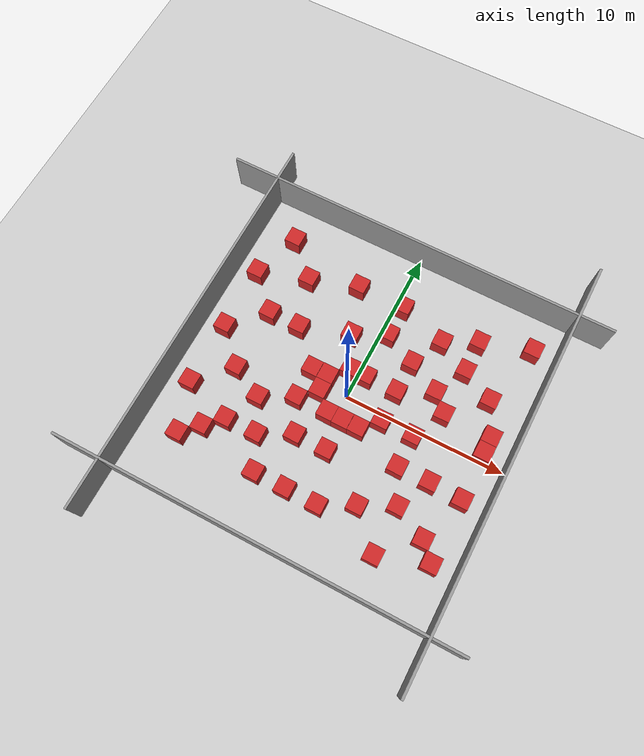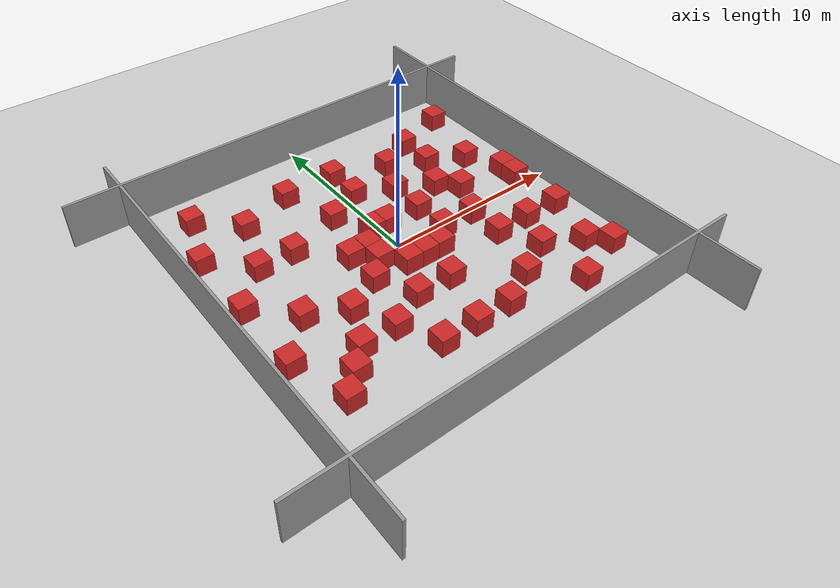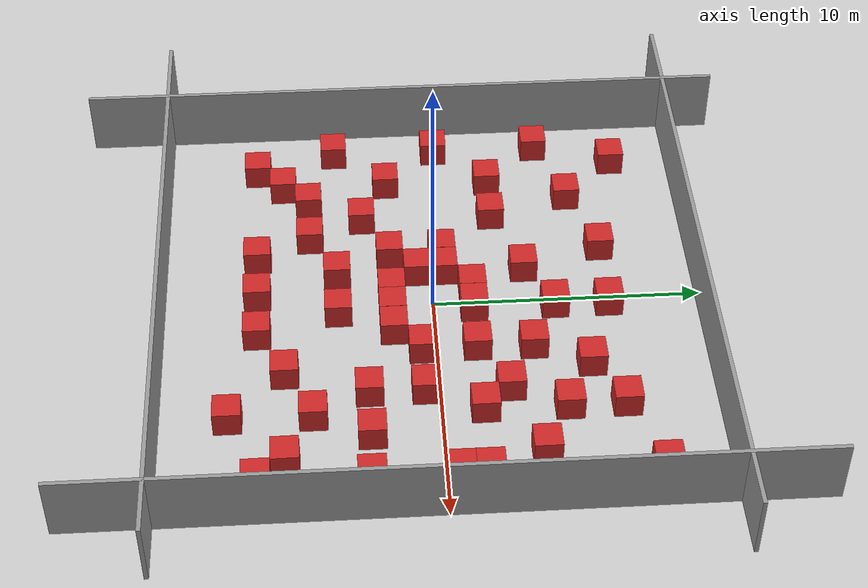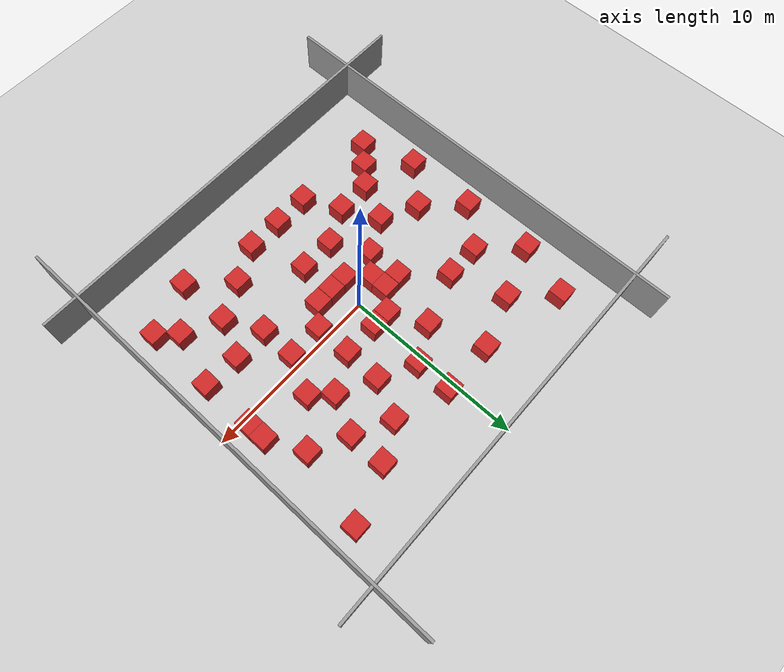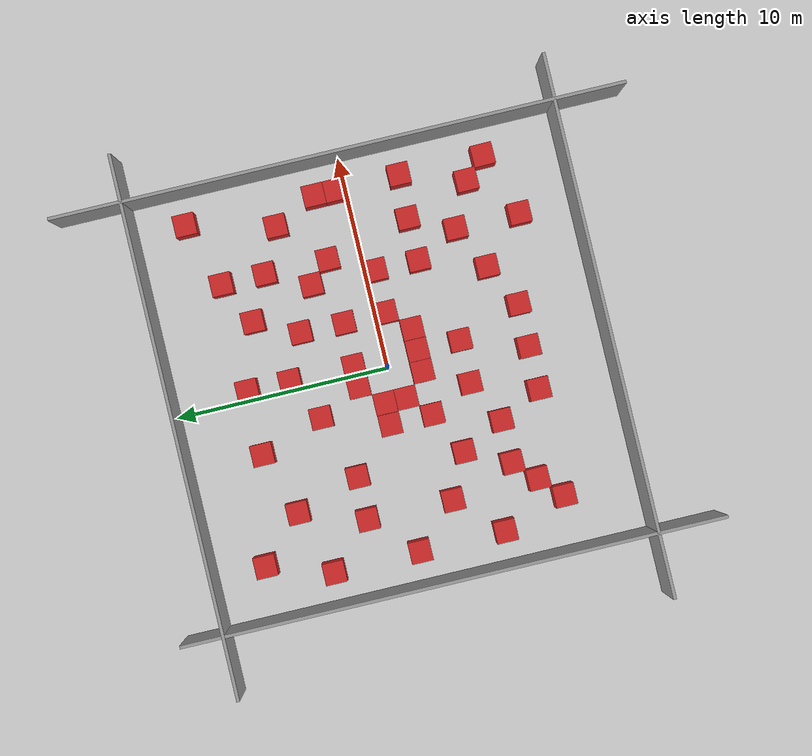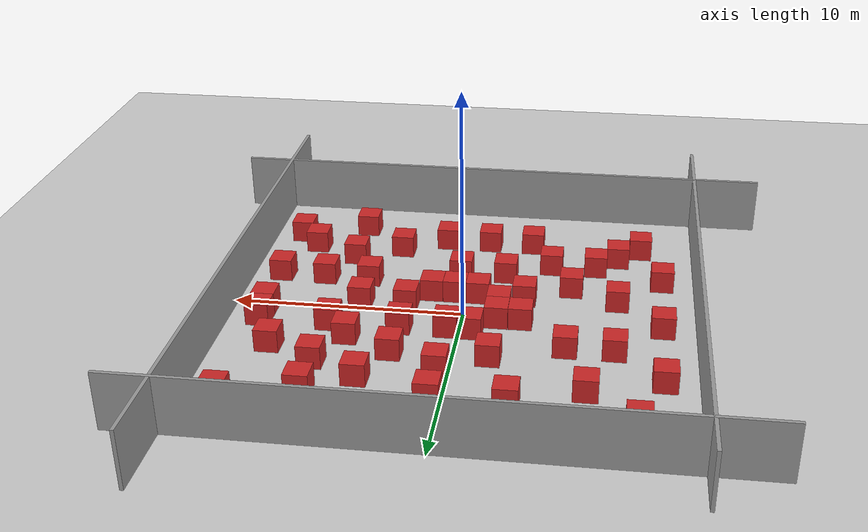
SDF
<sdf version="1.7">
 <world name="default">
  <light name="sun" type="directional">
   <pose>0 0 10 0 -0 0</pose>
   <diffuse>0.8 0.8 0.8 1</diffuse>
   <specular>0.2 0.2 0.2 1</specular>
   <attenuation>
    <range>1000</range>
    <constant>0.9</constant>
    <linear>0.01</linear>
    <quadratic>0.001</quadratic>
   </attenuation>
   <direction>-0.5 0.1 -0.9</direction>
   <spot><inner_angle>0</inner_angle><outer_angle>0</outer_angle><falloff>0</falloff></spot>
  </light>
  <model name="ground_plane">
   <static>1</static>
   <link name="link">
    <collision name="collision">
     <geometry><plane><normal>0 0 1</normal><size>100 100</size></plane></geometry>
     <surface><friction><ode><mu>100</mu><mu2>50</mu2></ode></friction></surface>
    </collision>
    <visual name="visual">
     <cast_shadows>0</cast_shadows>
     <geometry><plane><normal>0 0 1</normal><size>100 100</size></plane></geometry>
     <material>
      <script><uri>file://media/materials/scripts/gazebo.material</uri><name>Gazebo/Grey</name></script>
     </material>
    </visual>
   </link>
  </model>
  <gravity>0 0 -9.8</gravity>
  <magnetic_field>6e-06 2.3e-05 -4.2e-05</magnetic_field>
  <atmosphere type="adiabatic"/>
  <physics type="ode">
   <max_step_size>0.001</max_step_size>
   <real_time_factor>1</real_time_factor>
   <real_time_update_rate>1000</real_time_update_rate>
  </physics>
  <scene><ambient>0.4 0.4 0.4 1</ambient><background>0.7 0.7 0.7 1</background><shadows>1</shadows></scene>
  <audio><device>default</device></audio>
  <spherical_coordinates>
   <surface_model>EARTH_WGS84</surface_model>
   <latitude_deg>0</latitude_deg>
   <longitude_deg>0</longitude_deg>
   <elevation>0</elevation>
   <heading_deg>0</heading_deg>
  </spherical_coordinates>
  <model name="unit_box_red_0">
   <link name="link">
    <inertial>
     <mass>1</mass>
     <inertia>
      <ixx>0.166667</ixx>
      <ixy>0</ixy>
      <ixz>0</ixz>
      <iyy>0.166667</iyy>
      <iyz>0</iyz>
      <izz>0.166667</izz>
     </inertia>
    </inertial>
    <visual name="visual">
     <geometry><box><size>1 1 1</size></box></geometry>
     <material>
      <script><name>Gazebo/Red</name><uri>file://media/materials/scripts/gazebo.material</uri></script>
      <shader type="pixel"><normal_map>__default__</normal_map></shader>
      <ambient>1 0 0 1</ambient>
      <diffuse>1 0 0 1</diffuse>
      <specular>1 0 0 1</specular>
      <emissive>1 0 0 1</emissive>
     </material>
    </visual>
    <collision name="collision">
     <geometry><box><size>1 1 1</size></box></geometry>
     <surface>
      <friction>
       <ode><mu>1</mu><mu2>1</mu2><fdir1>0 0 0</fdir1><slip1>0</slip1><slip2>0</slip2></ode>
       <torsional>
        <coefficient>1</coefficient>
        <patch_radius>0</patch_radius>
        <surface_radius>0</surface_radius>
        <use_patch_radius>1</use_patch_radius>
        <ode><slip>0</slip></ode>
       </torsional>
      </friction>
      <bounce><restitution_coefficient>0</restitution_coefficient><threshold>1e+06</threshold></bounce>
      <contact>
       <collide_without_contact>0</collide_without_contact>
       <collide_without_contact_bitmask>1</collide_without_contact_bitmask>
       <collide_bitmask>1</collide_bitmask>
       <ode>
        <soft_cfm>0</soft_cfm>
        <soft_erp>0.2</soft_erp>
        <kp>1e+13</kp>
        <kd>1</kd>
        <max_vel>0.01</max_vel>
        <min_depth>0</min_depth>
       </ode>
       <bullet>
        <split_impulse>1</split_impulse>
        <split_impulse_penetration_threshold>-0.01</split_impulse_penetration_threshold>
        <soft_cfm>0</soft_cfm>
        <soft_erp>0.2</soft_erp>
        <kp>1e+13</kp>
        <kd>1</kd>
       </bullet>
      </contact>
     </surface>
    </collision>
   </link>
   <static>0</static>
   <pose>2.51351 -0.508621 0.499995 0 1e-05 0</pose>
  </model>
  <model name="unit_box_red_0_clone">
   <link name="link">
    <inertial>
     <mass>1</mass>
     <inertia>
      <ixx>0.166667</ixx>
      <ixy>0</ixy>
      <ixz>0</ixz>
      <iyy>0.166667</iyy>
      <iyz>0</iyz>
      <izz>0.166667</izz>
     </inertia>
    </inertial>
    <visual name="visual">
     <geometry><box><size>1 1 1</size></box></geometry>
     <material>
      <script><name>Gazebo/Red</name><uri>file://media/materials/scripts/gazebo.material</uri></script>
      <shader type="pixel"><normal_map>__default__</normal_map></shader>
      <ambient>1 0 0 1</ambient>
      <diffuse>1 0 0 1</diffuse>
      <specular>1 0 0 1</specular>
      <emissive>1 0 0 1</emissive>
     </material>
    </visual>
    <collision name="collision">
     <geometry><box><size>1 1 1</size></box></geometry>
     <surface>
      <friction>
       <ode><mu>1</mu><mu2>1</mu2><fdir1>0 0 0</fdir1><slip1>0</slip1><slip2>0</slip2></ode>
       <torsional>
        <coefficient>1</coefficient>
        <patch_radius>0</patch_radius>
        <surface_radius>0</surface_radius>
        <use_patch_radius>1</use_patch_radius>
        <ode><slip>0</slip></ode>
       </torsional>
      </friction>
      <bounce><restitution_coefficient>0</restitution_coefficient><threshold>1e+06</threshold></bounce>
      <contact>
       <collide_without_contact>0</collide_without_contact>
       <collide_without_contact_bitmask>1</collide_without_contact_bitmask>
       <collide_bitmask>1</collide_bitmask>
       <ode>
        <soft_cfm>0</soft_cfm>
        <soft_erp>0.2</soft_erp>
        <kp>1e+13</kp>
        <kd>1</kd>
        <max_vel>0.01</max_vel>
        <min_depth>0</min_depth>
       </ode>
       <bullet>
        <split_impulse>1</split_impulse>
        <split_impulse_penetration_threshold>-0.01</split_impulse_penetration_threshold>
        <soft_cfm>0</soft_cfm>
        <soft_erp>0.2</soft_erp>
        <kp>1e+13</kp>
        <kd>1</kd>
       </bullet>
      </contact>
     </surface>
    </collision>
   </link>
   <static>0</static>
   <pose>0.486456 1.49281 0.499995 0 1e-05 0</pose>
  </model>
  <model name="unit_box_red_0_clone_0">
   <link name="link">
    <inertial>
     <mass>1</mass>
     <inertia>
      <ixx>0.166667</ixx>
      <ixy>0</ixy>
      <ixz>0</ixz>
      <iyy>0.166667</iyy>
      <iyz>0</iyz>
      <izz>0.166667</izz>
     </inertia>
    </inertial>
    <visual name="visual">
     <geometry><box><size>1 1 1</size></box></geometry>
     <material>
      <script><name>Gazebo/Red</name><uri>file://media/materials/scripts/gazebo.material</uri></script>
      <shader type="pixel"><normal_map>__default__</normal_map></shader>
      <ambient>1 0 0 1</ambient>
      <diffuse>1 0 0 1</diffuse>
      <specular>1 0 0 1</specular>
      <emissive>1 0 0 1</emissive>
     </material>
    </visual>
    <collision name="collision">
     <geometry><box><size>1 1 1</size></box></geometry>
     <surface>
      <friction>
       <ode><mu>1</mu><mu2>1</mu2><fdir1>0 0 0</fdir1><slip1>0</slip1><slip2>0</slip2></ode>
       <torsional>
        <coefficient>1</coefficient>
        <patch_radius>0</patch_radius>
        <surface_radius>0</surface_radius>
        <use_patch_radius>1</use_patch_radius>
        <ode><slip>0</slip></ode>
       </torsional>
      </friction>
      <bounce><restitution_coefficient>0</restitution_coefficient><threshold>1e+06</threshold></bounce>
      <contact>
       <collide_without_contact>0</collide_without_contact>
       <collide_without_contact_bitmask>1</collide_without_contact_bitmask>
       <collide_bitmask>1</collide_bitmask>
       <ode>
        <soft_cfm>0</soft_cfm>
        <soft_erp>0.2</soft_erp>
        <kp>1e+13</kp>
        <kd>1</kd>
        <max_vel>0.01</max_vel>
        <min_depth>0</min_depth>
       </ode>
       <bullet>
        <split_impulse>1</split_impulse>
        <split_impulse_penetration_threshold>-0.01</split_impulse_penetration_threshold>
        <soft_cfm>0</soft_cfm>
        <soft_erp>0.2</soft_erp>
        <kp>1e+13</kp>
        <kd>1</kd>
       </bullet>
      </contact>
     </surface>
    </collision>
   </link>
   <static>0</static>
   <pose>2.47641 1.46765 0.499995 0 1e-05 0</pose>
  </model>
  <model name="unit_box_red_0_clone_1">
   <link name="link">
    <inertial>
     <mass>1</mass>
     <inertia>
      <ixx>0.166667</ixx>
      <ixy>0</ixy>
      <ixz>0</ixz>
      <iyy>0.166667</iyy>
      <iyz>0</iyz>
      <izz>0.166667</izz>
     </inertia>
    </inertial>
    <visual name="visual">
     <geometry><box><size>1 1 1</size></box></geometry>
     <material>
      <script><name>Gazebo/Red</name><uri>file://media/materials/scripts/gazebo.material</uri></script>
      <shader type="pixel"><normal_map>__default__</normal_map></shader>
      <ambient>1 0 0 1</ambient>
      <diffuse>1 0 0 1</diffuse>
      <specular>1 0 0 1</specular>
      <emissive>1 0 0 1</emissive>
     </material>
    </visual>
    <collision name="collision">
     <geometry><box><size>1 1 1</size></box></geometry>
     <surface>
      <friction>
       <ode><mu>1</mu><mu2>1</mu2><fdir1>0 0 0</fdir1><slip1>0</slip1><slip2>0</slip2></ode>
       <torsional>
        <coefficient>1</coefficient>
        <patch_radius>0</patch_radius>
        <surface_radius>0</surface_radius>
        <use_patch_radius>1</use_patch_radius>
        <ode><slip>0</slip></ode>
       </torsional>
      </friction>
      <bounce><restitution_coefficient>0</restitution_coefficient><threshold>1e+06</threshold></bounce>
      <contact>
       <collide_without_contact>0</collide_without_contact>
       <collide_without_contact_bitmask>1</collide_without_contact_bitmask>
       <collide_bitmask>1</collide_bitmask>
       <ode>
        <soft_cfm>0</soft_cfm>
        <soft_erp>0.2</soft_erp>
        <kp>1e+13</kp>
        <kd>1</kd>
        <max_vel>0.01</max_vel>
        <min_depth>0</min_depth>
       </ode>
       <bullet>
        <split_impulse>1</split_impulse>
        <split_impulse_penetration_threshold>-0.01</split_impulse_penetration_threshold>
        <soft_cfm>0</soft_cfm>
        <soft_erp>0.2</soft_erp>
        <kp>1e+13</kp>
        <kd>1</kd>
       </bullet>
      </contact>
     </surface>
    </collision>
   </link>
   <static>0</static>
   <pose>1.50873 -1.50432 0.499995 0 1e-05 0</pose>
  </model>
  <model name="unit_box_red_0_clone_2">
   <link name="link">
    <inertial>
     <mass>1</mass>
     <inertia>
      <ixx>0.166667</ixx>
      <ixy>0</ixy>
      <ixz>0</ixz>
      <iyy>0.166667</iyy>
      <iyz>0</iyz>
      <izz>0.166667</izz>
     </inertia>
    </inertial>
    <visual name="visual">
     <geometry><box><size>1 1 1</size></box></geometry>
     <material>
      <script><name>Gazebo/Red</name><uri>file://media/materials/scripts/gazebo.material</uri></script>
      <shader type="pixel"><normal_map>__default__</normal_map></shader>
      <ambient>1 0 0 1</ambient>
      <diffuse>1 0 0 1</diffuse>
      <specular>1 0 0 1</specular>
      <emissive>1 0 0 1</emissive>
     </material>
    </visual>
    <collision name="collision">
     <geometry><box><size>1 1 1</size></box></geometry>
     <surface>
      <friction>
       <ode><mu>1</mu><mu2>1</mu2><fdir1>0 0 0</fdir1><slip1>0</slip1><slip2>0</slip2></ode>
       <torsional>
        <coefficient>1</coefficient>
        <patch_radius>0</patch_radius>
        <surface_radius>0</surface_radius>
        <use_patch_radius>1</use_patch_radius>
        <ode><slip>0</slip></ode>
       </torsional>
      </friction>
      <bounce><restitution_coefficient>0</restitution_coefficient><threshold>1e+06</threshold></bounce>
      <contact>
       <collide_without_contact>0</collide_without_contact>
       <collide_without_contact_bitmask>1</collide_without_contact_bitmask>
       <collide_bitmask>1</collide_bitmask>
       <ode>
        <soft_cfm>0</soft_cfm>
        <soft_erp>0.2</soft_erp>
        <kp>1e+13</kp>
        <kd>1</kd>
        <max_vel>0.01</max_vel>
        <min_depth>0</min_depth>
       </ode>
       <bullet>
        <split_impulse>1</split_impulse>
        <split_impulse_penetration_threshold>-0.01</split_impulse_penetration_threshold>
        <soft_cfm>0</soft_cfm>
        <soft_erp>0.2</soft_erp>
        <kp>1e+13</kp>
        <kd>1</kd>
       </bullet>
      </contact>
     </surface>
    </collision>
   </link>
   <static>0</static>
   <pose>0.502623 -1.50954 0.499995 0 1e-05 0</pose>
  </model>
  <model name="unit_box_red_0_clone_3">
   <link name="link">
    <inertial>
     <mass>1</mass>
     <inertia>
      <ixx>0.166667</ixx>
      <ixy>0</ixy>
      <ixz>0</ixz>
      <iyy>0.166667</iyy>
      <iyz>0</iyz>
      <izz>0.166667</izz>
     </inertia>
    </inertial>
    <visual name="visual">
     <geometry><box><size>1 1 1</size></box></geometry>
     <material>
      <script><name>Gazebo/Red</name><uri>file://media/materials/scripts/gazebo.material</uri></script>
      <shader type="pixel"><normal_map>__default__</normal_map></shader>
      <ambient>1 0 0 1</ambient>
      <diffuse>1 0 0 1</diffuse>
      <specular>1 0 0 1</specular>
      <emissive>1 0 0 1</emissive>
     </material>
    </visual>
    <collision name="collision">
     <geometry><box><size>1 1 1</size></box></geometry>
     <surface>
      <friction>
       <ode><mu>1</mu><mu2>1</mu2><fdir1>0 0 0</fdir1><slip1>0</slip1><slip2>0</slip2></ode>
       <torsional>
        <coefficient>1</coefficient>
        <patch_radius>0</patch_radius>
        <surface_radius>0</surface_radius>
        <use_patch_radius>1</use_patch_radius>
        <ode><slip>0</slip></ode>
       </torsional>
      </friction>
      <bounce><restitution_coefficient>0</restitution_coefficient><threshold>1e+06</threshold></bounce>
      <contact>
       <collide_without_contact>0</collide_without_contact>
       <collide_without_contact_bitmask>1</collide_without_contact_bitmask>
       <collide_bitmask>1</collide_bitmask>
       <ode>
        <soft_cfm>0</soft_cfm>
        <soft_erp>0.2</soft_erp>
        <kp>1e+13</kp>
        <kd>1</kd>
        <max_vel>0.01</max_vel>
        <min_depth>0</min_depth>
       </ode>
       <bullet>
        <split_impulse>1</split_impulse>
        <split_impulse_penetration_threshold>-0.01</split_impulse_penetration_threshold>
        <soft_cfm>0</soft_cfm>
        <soft_erp>0.2</soft_erp>
        <kp>1e+13</kp>
        <kd>1</kd>
       </bullet>
      </contact>
     </surface>
    </collision>
   </link>
   <static>0</static>
   <pose>-1.50793 -0.508747 0.499995 -0 1e-05 0.000642</pose>
  </model>
  <model name="unit_box_red_0_clone_4">
   <link name="link">
    <inertial>
     <mass>1</mass>
     <inertia>
      <ixx>0.166667</ixx>
      <ixy>0</ixy>
      <ixz>0</ixz>
      <iyy>0.166667</iyy>
      <iyz>0</iyz>
      <izz>0.166667</izz>
     </inertia>
    </inertial>
    <visual name="visual">
     <geometry><box><size>1 1 1</size></box></geometry>
     <material>
      <script><name>Gazebo/Red</name><uri>file://media/materials/scripts/gazebo.material</uri></script>
      <shader type="pixel"><normal_map>__default__</normal_map></shader>
      <ambient>1 0 0 1</ambient>
      <diffuse>1 0 0 1</diffuse>
      <specular>1 0 0 1</specular>
      <emissive>1 0 0 1</emissive>
     </material>
    </visual>
    <collision name="collision">
     <geometry><box><size>1 1 1</size></box></geometry>
     <surface>
      <friction>
       <ode><mu>1</mu><mu2>1</mu2><fdir1>0 0 0</fdir1><slip1>0</slip1><slip2>0</slip2></ode>
       <torsional>
        <coefficient>1</coefficient>
        <patch_radius>0</patch_radius>
        <surface_radius>0</surface_radius>
        <use_patch_radius>1</use_patch_radius>
        <ode><slip>0</slip></ode>
       </torsional>
      </friction>
      <bounce><restitution_coefficient>0</restitution_coefficient><threshold>1e+06</threshold></bounce>
      <contact>
       <collide_without_contact>0</collide_without_contact>
       <collide_without_contact_bitmask>1</collide_without_contact_bitmask>
       <collide_bitmask>1</collide_bitmask>
       <ode>
        <soft_cfm>0</soft_cfm>
        <soft_erp>0.2</soft_erp>
        <kp>1e+13</kp>
        <kd>1</kd>
        <max_vel>0.01</max_vel>
        <min_depth>0</min_depth>
       </ode>
       <bullet>
        <split_impulse>1</split_impulse>
        <split_impulse_penetration_threshold>-0.01</split_impulse_penetration_threshold>
        <soft_cfm>0</soft_cfm>
        <soft_erp>0.2</soft_erp>
        <kp>1e+13</kp>
        <kd>1</kd>
       </bullet>
      </contact>
     </surface>
    </collision>
   </link>
   <static>0</static>
   <pose>-1.51509 0.49126 0.499995 -0 -1e-05 0.000645</pose>
  </model>
  <model name="unit_box_red_0_clone_5">
   <link name="link">
    <inertial>
     <mass>1</mass>
     <inertia>
      <ixx>0.166667</ixx>
      <ixy>0</ixy>
      <ixz>0</ixz>
      <iyy>0.166667</iyy>
      <iyz>0</iyz>
      <izz>0.166667</izz>
     </inertia>
    </inertial>
    <visual name="visual">
     <geometry><box><size>1 1 1</size></box></geometry>
     <material>
      <script><name>Gazebo/Red</name><uri>file://media/materials/scripts/gazebo.material</uri></script>
      <shader type="pixel"><normal_map>__default__</normal_map></shader>
      <ambient>1 0 0 1</ambient>
      <diffuse>1 0 0 1</diffuse>
      <specular>1 0 0 1</specular>
      <emissive>1 0 0 1</emissive>
     </material>
    </visual>
    <collision name="collision">
     <geometry><box><size>1 1 1</size></box></geometry>
     <surface>
      <friction>
       <ode><mu>1</mu><mu2>1</mu2><fdir1>0 0 0</fdir1><slip1>0</slip1><slip2>0</slip2></ode>
       <torsional>
        <coefficient>1</coefficient>
        <patch_radius>0</patch_radius>
        <surface_radius>0</surface_radius>
        <use_patch_radius>1</use_patch_radius>
        <ode><slip>0</slip></ode>
       </torsional>
      </friction>
      <bounce><restitution_coefficient>0</restitution_coefficient><threshold>1e+06</threshold></bounce>
      <contact>
       <collide_without_contact>0</collide_without_contact>
       <collide_without_contact_bitmask>1</collide_without_contact_bitmask>
       <collide_bitmask>1</collide_bitmask>
       <ode>
        <soft_cfm>0</soft_cfm>
        <soft_erp>0.2</soft_erp>
        <kp>1e+13</kp>
        <kd>1</kd>
        <max_vel>0.01</max_vel>
        <min_depth>0</min_depth>
       </ode>
       <bullet>
        <split_impulse>1</split_impulse>
        <split_impulse_penetration_threshold>-0.01</split_impulse_penetration_threshold>
        <soft_cfm>0</soft_cfm>
        <soft_erp>0.2</soft_erp>
        <kp>1e+13</kp>
        <kd>1</kd>
       </bullet>
      </contact>
     </surface>
    </collision>
   </link>
   <static>0</static>
   <pose>4.5201 2.5135 0.499995 0 1e-05 0.006824</pose>
  </model>
  <model name="unit_box_red_0_clone_6">
   <link name="link">
    <inertial>
     <mass>1</mass>
     <inertia>
      <ixx>0.166667</ixx>
      <ixy>0</ixy>
      <ixz>0</ixz>
      <iyy>0.166667</iyy>
      <iyz>0</iyz>
      <izz>0.166667</izz>
     </inertia>
    </inertial>
    <visual name="visual">
     <geometry><box><size>1 1 1</size></box></geometry>
     <material>
      <script><name>Gazebo/Red</name><uri>file://media/materials/scripts/gazebo.material</uri></script>
      <shader type="pixel"><normal_map>__default__</normal_map></shader>
      <ambient>1 0 0 1</ambient>
      <diffuse>1 0 0 1</diffuse>
      <specular>1 0 0 1</specular>
      <emissive>1 0 0 1</emissive>
     </material>
    </visual>
    <collision name="collision">
     <geometry><box><size>1 1 1</size></box></geometry>
     <surface>
      <friction>
       <ode><mu>1</mu><mu2>1</mu2><fdir1>0 0 0</fdir1><slip1>0</slip1><slip2>0</slip2></ode>
       <torsional>
        <coefficient>1</coefficient>
        <patch_radius>0</patch_radius>
        <surface_radius>0</surface_radius>
        <use_patch_radius>1</use_patch_radius>
        <ode><slip>0</slip></ode>
       </torsional>
      </friction>
      <bounce><restitution_coefficient>0</restitution_coefficient><threshold>1e+06</threshold></bounce>
      <contact>
       <collide_without_contact>0</collide_without_contact>
       <collide_without_contact_bitmask>1</collide_without_contact_bitmask>
       <collide_bitmask>1</collide_bitmask>
       <ode>
        <soft_cfm>0</soft_cfm>
        <soft_erp>0.2</soft_erp>
        <kp>1e+13</kp>
        <kd>1</kd>
        <max_vel>0.01</max_vel>
        <min_depth>0</min_depth>
       </ode>
       <bullet>
        <split_impulse>1</split_impulse>
        <split_impulse_penetration_threshold>-0.01</split_impulse_penetration_threshold>
        <soft_cfm>0</soft_cfm>
        <soft_erp>0.2</soft_erp>
        <kp>1e+13</kp>
        <kd>1</kd>
       </bullet>
      </contact>
     </surface>
    </collision>
   </link>
   <static>0</static>
   <pose>5.48575 1.52037 0.499995 0 -1e-05 0.007591</pose>
  </model>
  <model name="unit_box_red_0_clone_7">
   <link name="link">
    <inertial>
     <mass>1</mass>
     <inertia>
      <ixx>0.166667</ixx>
      <ixy>0</ixy>
      <ixz>0</ixz>
      <iyy>0.166667</iyy>
      <iyz>0</iyz>
      <izz>0.166667</izz>
     </inertia>
    </inertial>
    <visual name="visual">
     <geometry><box><size>1 1 1</size></box></geometry>
     <material>
      <script><name>Gazebo/Red</name><uri>file://media/materials/scripts/gazebo.material</uri></script>
      <shader type="pixel"><normal_map>__default__</normal_map></shader>
      <ambient>1 0 0 1</ambient>
      <diffuse>1 0 0 1</diffuse>
      <specular>1 0 0 1</specular>
      <emissive>1 0 0 1</emissive>
     </material>
    </visual>
    <collision name="collision">
     <geometry><box><size>1 1 1</size></box></geometry>
     <surface>
      <friction>
       <ode><mu>1</mu><mu2>1</mu2><fdir1>0 0 0</fdir1><slip1>0</slip1><slip2>0</slip2></ode>
       <torsional>
        <coefficient>1</coefficient>
        <patch_radius>0</patch_radius>
        <surface_radius>0</surface_radius>
        <use_patch_radius>1</use_patch_radius>
        <ode><slip>0</slip></ode>
       </torsional>
      </friction>
      <bounce><restitution_coefficient>0</restitution_coefficient><threshold>1e+06</threshold></bounce>
      <contact>
       <collide_without_contact>0</collide_without_contact>
       <collide_without_contact_bitmask>1</collide_without_contact_bitmask>
       <collide_bitmask>1</collide_bitmask>
       <ode>
        <soft_cfm>0</soft_cfm>
        <soft_erp>0.2</soft_erp>
        <kp>1e+13</kp>
        <kd>1</kd>
        <max_vel>0.01</max_vel>
        <min_depth>0</min_depth>
       </ode>
       <bullet>
        <split_impulse>1</split_impulse>
        <split_impulse_penetration_threshold>-0.01</split_impulse_penetration_threshold>
        <soft_cfm>0</soft_cfm>
        <soft_erp>0.2</soft_erp>
        <kp>1e+13</kp>
        <kd>1</kd>
       </bullet>
      </contact>
     </surface>
    </collision>
   </link>
   <static>0</static>
   <pose>2.51729 3.51054 0.499995 0 1e-05 0</pose>
  </model>
  <model name="unit_box_red_0_clone_8">
   <link name="link">
    <inertial>
     <mass>1</mass>
     <inertia>
      <ixx>0.166667</ixx>
      <ixy>0</ixy>
      <ixz>0</ixz>
      <iyy>0.166667</iyy>
      <iyz>0</iyz>
      <izz>0.166667</izz>
     </inertia>
    </inertial>
    <visual name="visual">
     <geometry><box><size>1 1 1</size></box></geometry>
     <material>
      <script><name>Gazebo/Red</name><uri>file://media/materials/scripts/gazebo.material</uri></script>
      <shader type="pixel"><normal_map>__default__</normal_map></shader>
      <ambient>1 0 0 1</ambient>
      <diffuse>1 0 0 1</diffuse>
      <specular>1 0 0 1</specular>
      <emissive>1 0 0 1</emissive>
     </material>
    </visual>
    <collision name="collision">
     <geometry><box><size>1 1 1</size></box></geometry>
     <surface>
      <friction>
       <ode><mu>1</mu><mu2>1</mu2><fdir1>0 0 0</fdir1><slip1>0</slip1><slip2>0</slip2></ode>
       <torsional>
        <coefficient>1</coefficient>
        <patch_radius>0</patch_radius>
        <surface_radius>0</surface_radius>
        <use_patch_radius>1</use_patch_radius>
        <ode><slip>0</slip></ode>
       </torsional>
      </friction>
      <bounce><restitution_coefficient>0</restitution_coefficient><threshold>1e+06</threshold></bounce>
      <contact>
       <collide_without_contact>0</collide_without_contact>
       <collide_without_contact_bitmask>1</collide_without_contact_bitmask>
       <collide_bitmask>1</collide_bitmask>
       <ode>
        <soft_cfm>0</soft_cfm>
        <soft_erp>0.2</soft_erp>
        <kp>1e+13</kp>
        <kd>1</kd>
        <max_vel>0.01</max_vel>
        <min_depth>0</min_depth>
       </ode>
       <bullet>
        <split_impulse>1</split_impulse>
        <split_impulse_penetration_threshold>-0.01</split_impulse_penetration_threshold>
        <soft_cfm>0</soft_cfm>
        <soft_erp>0.2</soft_erp>
        <kp>1e+13</kp>
        <kd>1</kd>
       </bullet>
      </contact>
     </surface>
    </collision>
   </link>
   <static>0</static>
   <pose>0.488659 4.49142 0.499995 0 1e-05 0</pose>
  </model>
  <model name="unit_box_red_0_clone_9">
   <link name="link">
    <inertial>
     <mass>1</mass>
     <inertia>
      <ixx>0.166667</ixx>
      <ixy>0</ixy>
      <ixz>0</ixz>
      <iyy>0.166667</iyy>
      <iyz>0</iyz>
      <izz>0.166667</izz>
     </inertia>
    </inertial>
    <visual name="visual">
     <geometry><box><size>1 1 1</size></box></geometry>
     <material>
      <script><name>Gazebo/Red</name><uri>file://media/materials/scripts/gazebo.material</uri></script>
      <shader type="pixel"><normal_map>__default__</normal_map></shader>
      <ambient>1 0 0 1</ambient>
      <diffuse>1 0 0 1</diffuse>
      <specular>1 0 0 1</specular>
      <emissive>1 0 0 1</emissive>
     </material>
    </visual>
    <collision name="collision">
     <geometry><box><size>1 1 1</size></box></geometry>
     <surface>
      <friction>
       <ode><mu>1</mu><mu2>1</mu2><fdir1>0 0 0</fdir1><slip1>0</slip1><slip2>0</slip2></ode>
       <torsional>
        <coefficient>1</coefficient>
        <patch_radius>0</patch_radius>
        <surface_radius>0</surface_radius>
        <use_patch_radius>1</use_patch_radius>
        <ode><slip>0</slip></ode>
       </torsional>
      </friction>
      <bounce><restitution_coefficient>0</restitution_coefficient><threshold>1e+06</threshold></bounce>
      <contact>
       <collide_without_contact>0</collide_without_contact>
       <collide_without_contact_bitmask>1</collide_without_contact_bitmask>
       <collide_bitmask>1</collide_bitmask>
       <ode>
        <soft_cfm>0</soft_cfm>
        <soft_erp>0.2</soft_erp>
        <kp>1e+13</kp>
        <kd>1</kd>
        <max_vel>0.01</max_vel>
        <min_depth>0</min_depth>
       </ode>
       <bullet>
        <split_impulse>1</split_impulse>
        <split_impulse_penetration_threshold>-0.01</split_impulse_penetration_threshold>
        <soft_cfm>0</soft_cfm>
        <soft_erp>0.2</soft_erp>
        <kp>1e+13</kp>
        <kd>1</kd>
       </bullet>
      </contact>
     </surface>
    </collision>
   </link>
   <static>0</static>
   <pose>-1.4954 3.48826 0.499995 0 1e-05 0</pose>
  </model>
  <model name="unit_box_red_0_clone_10">
   <link name="link">
    <inertial>
     <mass>1</mass>
     <inertia>
      <ixx>0.166667</ixx>
      <ixy>0</ixy>
      <ixz>0</ixz>
      <iyy>0.166667</iyy>
      <iyz>0</iyz>
      <izz>0.166667</izz>
     </inertia>
    </inertial>
    <visual name="visual">
     <geometry><box><size>1 1 1</size></box></geometry>
     <material>
      <script><name>Gazebo/Red</name><uri>file://media/materials/scripts/gazebo.material</uri></script>
      <shader type="pixel"><normal_map>__default__</normal_map></shader>
      <ambient>1 0 0 1</ambient>
      <diffuse>1 0 0 1</diffuse>
      <specular>1 0 0 1</specular>
      <emissive>1 0 0 1</emissive>
     </material>
    </visual>
    <collision name="collision">
     <geometry><box><size>1 1 1</size></box></geometry>
     <surface>
      <friction>
       <ode><mu>1</mu><mu2>1</mu2><fdir1>0 0 0</fdir1><slip1>0</slip1><slip2>0</slip2></ode>
       <torsional>
        <coefficient>1</coefficient>
        <patch_radius>0</patch_radius>
        <surface_radius>0</surface_radius>
        <use_patch_radius>1</use_patch_radius>
        <ode><slip>0</slip></ode>
       </torsional>
      </friction>
      <bounce><restitution_coefficient>0</restitution_coefficient><threshold>1e+06</threshold></bounce>
      <contact>
       <collide_without_contact>0</collide_without_contact>
       <collide_without_contact_bitmask>1</collide_without_contact_bitmask>
       <collide_bitmask>1</collide_bitmask>
       <ode>
        <soft_cfm>0</soft_cfm>
        <soft_erp>0.2</soft_erp>
        <kp>1e+13</kp>
        <kd>1</kd>
        <max_vel>0.01</max_vel>
        <min_depth>0</min_depth>
       </ode>
       <bullet>
        <split_impulse>1</split_impulse>
        <split_impulse_penetration_threshold>-0.01</split_impulse_penetration_threshold>
        <soft_cfm>0</soft_cfm>
        <soft_erp>0.2</soft_erp>
        <kp>1e+13</kp>
        <kd>1</kd>
       </bullet>
      </contact>
     </surface>
    </collision>
   </link>
   <static>0</static>
   <pose>-2.52511 0.481594 0.499995 -1e-05 0 0.000645</pose>
  </model>
  <model name="unit_box_red_0_clone_11">
   <link name="link">
    <inertial>
     <mass>1</mass>
     <inertia>
      <ixx>0.166667</ixx>
      <ixy>0</ixy>
      <ixz>0</ixz>
      <iyy>0.166667</iyy>
      <iyz>0</iyz>
      <izz>0.166667</izz>
     </inertia>
    </inertial>
    <visual name="visual">
     <geometry><box><size>1 1 1</size></box></geometry>
     <material>
      <script><name>Gazebo/Red</name><uri>file://media/materials/scripts/gazebo.material</uri></script>
      <shader type="pixel"><normal_map>__default__</normal_map></shader>
      <ambient>1 0 0 1</ambient>
      <diffuse>1 0 0 1</diffuse>
      <specular>1 0 0 1</specular>
      <emissive>1 0 0 1</emissive>
     </material>
    </visual>
    <collision name="collision">
     <geometry><box><size>1 1 1</size></box></geometry>
     <surface>
      <friction>
       <ode><mu>1</mu><mu2>1</mu2><fdir1>0 0 0</fdir1><slip1>0</slip1><slip2>0</slip2></ode>
       <torsional>
        <coefficient>1</coefficient>
        <patch_radius>0</patch_radius>
        <surface_radius>0</surface_radius>
        <use_patch_radius>1</use_patch_radius>
        <ode><slip>0</slip></ode>
       </torsional>
      </friction>
      <bounce><restitution_coefficient>0</restitution_coefficient><threshold>1e+06</threshold></bounce>
      <contact>
       <collide_without_contact>0</collide_without_contact>
       <collide_without_contact_bitmask>1</collide_without_contact_bitmask>
       <collide_bitmask>1</collide_bitmask>
       <ode>
        <soft_cfm>0</soft_cfm>
        <soft_erp>0.2</soft_erp>
        <kp>1e+13</kp>
        <kd>1</kd>
        <max_vel>0.01</max_vel>
        <min_depth>0</min_depth>
       </ode>
       <bullet>
        <split_impulse>1</split_impulse>
        <split_impulse_penetration_threshold>-0.01</split_impulse_penetration_threshold>
        <soft_cfm>0</soft_cfm>
        <soft_erp>0.2</soft_erp>
        <kp>1e+13</kp>
        <kd>1</kd>
       </bullet>
      </contact>
     </surface>
    </collision>
   </link>
   <static>0</static>
   <pose>-2.52086 -1.50531 0.499995 0 1e-05 0</pose>
  </model>
  <model name="unit_box_red_0_clone_12">
   <link name="link">
    <inertial>
     <mass>1</mass>
     <inertia>
      <ixx>0.166667</ixx>
      <ixy>0</ixy>
      <ixz>0</ixz>
      <iyy>0.166667</iyy>
      <iyz>0</iyz>
      <izz>0.166667</izz>
     </inertia>
    </inertial>
    <visual name="visual">
     <geometry><box><size>1 1 1</size></box></geometry>
     <material>
      <script><name>Gazebo/Red</name><uri>file://media/materials/scripts/gazebo.material</uri></script>
      <shader type="pixel"><normal_map>__default__</normal_map></shader>
      <ambient>1 0 0 1</ambient>
      <diffuse>1 0 0 1</diffuse>
      <specular>1 0 0 1</specular>
      <emissive>1 0 0 1</emissive>
     </material>
    </visual>
    <collision name="collision">
     <geometry><box><size>1 1 1</size></box></geometry>
     <surface>
      <friction>
       <ode><mu>1</mu><mu2>1</mu2><fdir1>0 0 0</fdir1><slip1>0</slip1><slip2>0</slip2></ode>
       <torsional>
        <coefficient>1</coefficient>
        <patch_radius>0</patch_radius>
        <surface_radius>0</surface_radius>
        <use_patch_radius>1</use_patch_radius>
        <ode><slip>0</slip></ode>
       </torsional>
      </friction>
      <bounce><restitution_coefficient>0</restitution_coefficient><threshold>1e+06</threshold></bounce>
      <contact>
       <collide_without_contact>0</collide_without_contact>
       <collide_without_contact_bitmask>1</collide_without_contact_bitmask>
       <collide_bitmask>1</collide_bitmask>
       <ode>
        <soft_cfm>0</soft_cfm>
        <soft_erp>0.2</soft_erp>
        <kp>1e+13</kp>
        <kd>1</kd>
        <max_vel>0.01</max_vel>
        <min_depth>0</min_depth>
       </ode>
       <bullet>
        <split_impulse>1</split_impulse>
        <split_impulse_penetration_threshold>-0.01</split_impulse_penetration_threshold>
        <soft_cfm>0</soft_cfm>
        <soft_erp>0.2</soft_erp>
        <kp>1e+13</kp>
        <kd>1</kd>
       </bullet>
      </contact>
     </surface>
    </collision>
   </link>
   <static>0</static>
   <pose>-1.51768 -3.51166 0.499995 0 1e-05 0</pose>
  </model>
  <model name="unit_box_red_0_clone_13">
   <link name="link">
    <inertial>
     <mass>1</mass>
     <inertia>
      <ixx>0.166667</ixx>
      <ixy>0</ixy>
      <ixz>0</ixz>
      <iyy>0.166667</iyy>
      <iyz>0</iyz>
      <izz>0.166667</izz>
     </inertia>
    </inertial>
    <visual name="visual">
     <geometry><box><size>1 1 1</size></box></geometry>
     <material>
      <script><name>Gazebo/Red</name><uri>file://media/materials/scripts/gazebo.material</uri></script>
      <shader type="pixel"><normal_map>__default__</normal_map></shader>
      <ambient>1 0 0 1</ambient>
      <diffuse>1 0 0 1</diffuse>
      <specular>1 0 0 1</specular>
      <emissive>1 0 0 1</emissive>
     </material>
    </visual>
    <collision name="collision">
     <geometry><box><size>1 1 1</size></box></geometry>
     <surface>
      <friction>
       <ode><mu>1</mu><mu2>1</mu2><fdir1>0 0 0</fdir1><slip1>0</slip1><slip2>0</slip2></ode>
       <torsional>
        <coefficient>1</coefficient>
        <patch_radius>0</patch_radius>
        <surface_radius>0</surface_radius>
        <use_patch_radius>1</use_patch_radius>
        <ode><slip>0</slip></ode>
       </torsional>
      </friction>
      <bounce><restitution_coefficient>0</restitution_coefficient><threshold>1e+06</threshold></bounce>
      <contact>
       <collide_without_contact>0</collide_without_contact>
       <collide_without_contact_bitmask>1</collide_without_contact_bitmask>
       <collide_bitmask>1</collide_bitmask>
       <ode>
        <soft_cfm>0</soft_cfm>
        <soft_erp>0.2</soft_erp>
        <kp>1e+13</kp>
        <kd>1</kd>
        <max_vel>0.01</max_vel>
        <min_depth>0</min_depth>
       </ode>
       <bullet>
        <split_impulse>1</split_impulse>
        <split_impulse_penetration_threshold>-0.01</split_impulse_penetration_threshold>
        <soft_cfm>0</soft_cfm>
        <soft_erp>0.2</soft_erp>
        <kp>1e+13</kp>
        <kd>1</kd>
       </bullet>
      </contact>
     </surface>
    </collision>
   </link>
   <static>0</static>
   <pose>0.488657 -3.51166 0.499995 0 1e-05 0</pose>
  </model>
  <model name="unit_box_red_0_clone_14">
   <link name="link">
    <inertial>
     <mass>1</mass>
     <inertia>
      <ixx>0.166667</ixx>
      <ixy>0</ixy>
      <ixz>0</ixz>
      <iyy>0.166667</iyy>
      <iyz>0</iyz>
      <izz>0.166667</izz>
     </inertia>
    </inertial>
    <visual name="visual">
     <geometry><box><size>1 1 1</size></box></geometry>
     <material>
      <script><name>Gazebo/Red</name><uri>file://media/materials/scripts/gazebo.material</uri></script>
      <shader type="pixel"><normal_map>__default__</normal_map></shader>
      <ambient>1 0 0 1</ambient>
      <diffuse>1 0 0 1</diffuse>
      <specular>1 0 0 1</specular>
      <emissive>1 0 0 1</emissive>
     </material>
    </visual>
    <collision name="collision">
     <geometry><box><size>1 1 1</size></box></geometry>
     <surface>
      <friction>
       <ode><mu>1</mu><mu2>1</mu2><fdir1>0 0 0</fdir1><slip1>0</slip1><slip2>0</slip2></ode>
       <torsional>
        <coefficient>1</coefficient>
        <patch_radius>0</patch_radius>
        <surface_radius>0</surface_radius>
        <use_patch_radius>1</use_patch_radius>
        <ode><slip>0</slip></ode>
       </torsional>
      </friction>
      <bounce><restitution_coefficient>0</restitution_coefficient><threshold>1e+06</threshold></bounce>
      <contact>
       <collide_without_contact>0</collide_without_contact>
       <collide_without_contact_bitmask>1</collide_without_contact_bitmask>
       <collide_bitmask>1</collide_bitmask>
       <ode>
        <soft_cfm>0</soft_cfm>
        <soft_erp>0.2</soft_erp>
        <kp>1e+13</kp>
        <kd>1</kd>
        <max_vel>0.01</max_vel>
        <min_depth>0</min_depth>
       </ode>
       <bullet>
        <split_impulse>1</split_impulse>
        <split_impulse_penetration_threshold>-0.01</split_impulse_penetration_threshold>
        <soft_cfm>0</soft_cfm>
        <soft_erp>0.2</soft_erp>
        <kp>1e+13</kp>
        <kd>1</kd>
       </bullet>
      </contact>
     </surface>
    </collision>
   </link>
   <static>0</static>
   <pose>5.50451 4.49142 0.499995 0 1e-05 0</pose>
  </model>
  <model name="unit_box_red_0_clone_15">
   <link name="link">
    <inertial>
     <mass>1</mass>
     <inertia>
      <ixx>0.166667</ixx>
      <ixy>0</ixy>
      <ixz>0</ixz>
      <iyy>0.166667</iyy>
      <iyz>0</iyz>
      <izz>0.166667</izz>
     </inertia>
    </inertial>
    <visual name="visual">
     <geometry><box><size>1 1 1</size></box></geometry>
     <material>
      <script><name>Gazebo/Red</name><uri>file://media/materials/scripts/gazebo.material</uri></script>
      <shader type="pixel"><normal_map>__default__</normal_map></shader>
      <ambient>1 0 0 1</ambient>
      <diffuse>1 0 0 1</diffuse>
      <specular>1 0 0 1</specular>
      <emissive>1 0 0 1</emissive>
     </material>
    </visual>
    <collision name="collision">
     <geometry><box><size>1 1 1</size></box></geometry>
     <surface>
      <friction>
       <ode><mu>1</mu><mu2>1</mu2><fdir1>0 0 0</fdir1><slip1>0</slip1><slip2>0</slip2></ode>
       <torsional>
        <coefficient>1</coefficient>
        <patch_radius>0</patch_radius>
        <surface_radius>0</surface_radius>
        <use_patch_radius>1</use_patch_radius>
        <ode><slip>0</slip></ode>
       </torsional>
      </friction>
      <bounce><restitution_coefficient>0</restitution_coefficient><threshold>1e+06</threshold></bounce>
      <contact>
       <collide_without_contact>0</collide_without_contact>
       <collide_without_contact_bitmask>1</collide_without_contact_bitmask>
       <collide_bitmask>1</collide_bitmask>
       <ode>
        <soft_cfm>0</soft_cfm>
        <soft_erp>0.2</soft_erp>
        <kp>1e+13</kp>
        <kd>1</kd>
        <max_vel>0.01</max_vel>
        <min_depth>0</min_depth>
       </ode>
       <bullet>
        <split_impulse>1</split_impulse>
        <split_impulse_penetration_threshold>-0.01</split_impulse_penetration_threshold>
        <soft_cfm>0</soft_cfm>
        <soft_erp>0.2</soft_erp>
        <kp>1e+13</kp>
        <kd>1</kd>
       </bullet>
      </contact>
     </surface>
    </collision>
   </link>
   <static>0</static>
   <pose>3.49817 5.51689 0.499995 0 1e-05 0</pose>
  </model>
  <model name="unit_box_red_0_clone_16">
   <link name="link">
    <inertial>
     <mass>1</mass>
     <inertia>
      <ixx>0.166667</ixx>
      <ixy>0</ixy>
      <ixz>0</ixz>
      <iyy>0.166667</iyy>
      <iyz>0</iyz>
      <izz>0.166667</izz>
     </inertia>
    </inertial>
    <visual name="visual">
     <geometry><box><size>1 1 1</size></box></geometry>
     <material>
      <script><name>Gazebo/Red</name><uri>file://media/materials/scripts/gazebo.material</uri></script>
      <shader type="pixel"><normal_map>__default__</normal_map></shader>
      <ambient>1 0 0 1</ambient>
      <diffuse>1 0 0 1</diffuse>
      <specular>1 0 0 1</specular>
      <emissive>1 0 0 1</emissive>
     </material>
    </visual>
    <collision name="collision">
     <geometry><box><size>1 1 1</size></box></geometry>
     <surface>
      <friction>
       <ode><mu>1</mu><mu2>1</mu2><fdir1>0 0 0</fdir1><slip1>0</slip1><slip2>0</slip2></ode>
       <torsional>
        <coefficient>1</coefficient>
        <patch_radius>0</patch_radius>
        <surface_radius>0</surface_radius>
        <use_patch_radius>1</use_patch_radius>
        <ode><slip>0</slip></ode>
       </torsional>
      </friction>
      <bounce><restitution_coefficient>0</restitution_coefficient><threshold>1e+06</threshold></bounce>
      <contact>
       <collide_without_contact>0</collide_without_contact>
       <collide_without_contact_bitmask>1</collide_without_contact_bitmask>
       <collide_bitmask>1</collide_bitmask>
       <ode>
        <soft_cfm>0</soft_cfm>
        <soft_erp>0.2</soft_erp>
        <kp>1e+13</kp>
        <kd>1</kd>
        <max_vel>0.01</max_vel>
        <min_depth>0</min_depth>
       </ode>
       <bullet>
        <split_impulse>1</split_impulse>
        <split_impulse_penetration_threshold>-0.01</split_impulse_penetration_threshold>
        <soft_cfm>0</soft_cfm>
        <soft_erp>0.2</soft_erp>
        <kp>1e+13</kp>
        <kd>1</kd>
       </bullet>
      </contact>
     </surface>
    </collision>
   </link>
   <static>0</static>
   <pose>5.48222 6.52006 0.499995 0 1e-05 0</pose>
  </model>
  <model name="unit_box_red_0_clone_17">
   <link name="link">
    <inertial>
     <mass>1</mass>
     <inertia>
      <ixx>0.166667</ixx>
      <ixy>0</ixy>
      <ixz>0</ixz>
      <iyy>0.166667</iyy>
      <iyz>0</iyz>
      <izz>0.166667</izz>
     </inertia>
    </inertial>
    <visual name="visual">
     <geometry><box><size>1 1 1</size></box></geometry>
     <material>
      <script><name>Gazebo/Red</name><uri>file://media/materials/scripts/gazebo.material</uri></script>
      <shader type="pixel"><normal_map>__default__</normal_map></shader>
      <ambient>1 0 0 1</ambient>
      <diffuse>1 0 0 1</diffuse>
      <specular>1 0 0 1</specular>
      <emissive>1 0 0 1</emissive>
     </material>
    </visual>
    <collision name="collision">
     <geometry><box><size>1 1 1</size></box></geometry>
     <surface>
      <friction>
       <ode><mu>1</mu><mu2>1</mu2><fdir1>0 0 0</fdir1><slip1>0</slip1><slip2>0</slip2></ode>
       <torsional>
        <coefficient>1</coefficient>
        <patch_radius>0</patch_radius>
        <surface_radius>0</surface_radius>
        <use_patch_radius>1</use_patch_radius>
        <ode><slip>0</slip></ode>
       </torsional>
      </friction>
      <bounce><restitution_coefficient>0</restitution_coefficient><threshold>1e+06</threshold></bounce>
      <contact>
       <collide_without_contact>0</collide_without_contact>
       <collide_without_contact_bitmask>1</collide_without_contact_bitmask>
       <collide_bitmask>1</collide_bitmask>
       <ode>
        <soft_cfm>0</soft_cfm>
        <soft_erp>0.2</soft_erp>
        <kp>1e+13</kp>
        <kd>1</kd>
        <max_vel>0.01</max_vel>
        <min_depth>0</min_depth>
       </ode>
       <bullet>
        <split_impulse>1</split_impulse>
        <split_impulse_penetration_threshold>-0.01</split_impulse_penetration_threshold>
        <soft_cfm>0</soft_cfm>
        <soft_erp>0.2</soft_erp>
        <kp>1e+13</kp>
        <kd>1</kd>
       </bullet>
      </contact>
     </surface>
    </collision>
   </link>
   <static>0</static>
   <pose>4.50134 -0.502145 0.499995 0 1e-05 0</pose>
  </model>
  <model name="unit_box_red_0_clone_21">
   <link name="link">
    <inertial>
     <mass>1</mass>
     <inertia>
      <ixx>0.166667</ixx>
      <ixy>0</ixy>
      <ixz>0</ixz>
      <iyy>0.166667</iyy>
      <iyz>0</iyz>
      <izz>0.166667</izz>
     </inertia>
    </inertial>
    <visual name="visual">
     <geometry><box><size>1 1 1</size></box></geometry>
     <material>
      <script><name>Gazebo/Red</name><uri>file://media/materials/scripts/gazebo.material</uri></script>
      <shader type="pixel"><normal_map>__default__</normal_map></shader>
      <ambient>1 0 0 1</ambient>
      <diffuse>1 0 0 1</diffuse>
      <specular>1 0 0 1</specular>
      <emissive>1 0 0 1</emissive>
     </material>
    </visual>
    <collision name="collision">
     <geometry><box><size>1 1 1</size></box></geometry>
     <surface>
      <friction>
       <ode><mu>1</mu><mu2>1</mu2><fdir1>0 0 0</fdir1><slip1>0</slip1><slip2>0</slip2></ode>
       <torsional>
        <coefficient>1</coefficient>
        <patch_radius>0</patch_radius>
        <surface_radius>0</surface_radius>
        <use_patch_radius>1</use_patch_radius>
        <ode><slip>0</slip></ode>
       </torsional>
      </friction>
      <bounce><restitution_coefficient>0</restitution_coefficient><threshold>1e+06</threshold></bounce>
      <contact>
       <collide_without_contact>0</collide_without_contact>
       <collide_without_contact_bitmask>1</collide_without_contact_bitmask>
       <collide_bitmask>1</collide_bitmask>
       <ode>
        <soft_cfm>0</soft_cfm>
        <soft_erp>0.2</soft_erp>
        <kp>1e+13</kp>
        <kd>1</kd>
        <max_vel>0.01</max_vel>
        <min_depth>0</min_depth>
       </ode>
       <bullet>
        <split_impulse>1</split_impulse>
        <split_impulse_penetration_threshold>-0.01</split_impulse_penetration_threshold>
        <soft_cfm>0</soft_cfm>
        <soft_erp>0.2</soft_erp>
        <kp>1e+13</kp>
        <kd>1</kd>
       </bullet>
      </contact>
     </surface>
    </collision>
   </link>
   <static>0</static>
   <pose>4.50061 -2.50401 0.499995 0 1e-05 0</pose>
  </model>
  <model name="wall_20x20">
   <pose>-0.40857 -0.043281 0 0 -0 0</pose>
   <link name="Wall_10">
    <collision name="Wall_10_Collision">
     <geometry><box><size>26.5 0.15 2.5</size></box></geometry>
     <pose>0 0 1.25 0 -0 0</pose>
    </collision>
    <visual name="Wall_10_Visual">
     <pose>0 0 1.25 0 -0 0</pose>
     <geometry><box><size>26.5 0.15 2.5</size></box></geometry>
     <material>
      <script><uri>file://media/materials/scripts/gazebo.material</uri><name>Gazebo/Grey</name></script>
      <ambient>1 1 1 1</ambient>
     </material>
     <meta><layer>0</layer></meta>
    </visual>
    <pose>10.3388 -0 0 0 -0 1.5708</pose>
   </link>
   <link name="Wall_4">
    <collision name="Wall_4_Collision">
     <geometry><box><size>25 0.15 2.5</size></box></geometry>
     <pose>0 0 1.25 0 -0 0</pose>
    </collision>
    <visual name="Wall_4_Visual">
     <pose>0 0 1.25 0 -0 0</pose>
     <geometry><box><size>25 0.15 2.5</size></box></geometry>
     <material>
      <script><uri>file://media/materials/scripts/gazebo.material</uri><name>Gazebo/Grey</name></script>
      <ambient>1 1 1 1</ambient>
     </material>
     <meta><layer>0</layer></meta>
    </visual>
    <pose>-0.041839 -9.9552 0 0 -0 0</pose>
   </link>
   <link name="Wall_6">
    <collision name="Wall_6_Collision">
     <geometry><box><size>25 0.15 2.5</size></box></geometry>
     <pose>0 0 1.25 0 -0 0</pose>
    </collision>
    <visual name="Wall_6_Visual">
     <pose>0 0 1.25 0 -0 0</pose>
     <geometry><box><size>25 0.15 2.5</size></box></geometry>
     <material>
      <script><uri>file://media/materials/scripts/gazebo.material</uri><name>Gazebo/Grey</name></script>
      <ambient>1 1 1 1</ambient>
     </material>
     <meta><layer>0</layer></meta>
    </visual>
    <pose>0.041839 9.9241 0 0 -0 0</pose>
   </link>
   <link name="Wall_8">
    <collision name="Wall_8_Collision">
     <geometry><box><size>25 0.15 2.5</size></box></geometry>
     <pose>0 0 1.25 0 -0 0</pose>
    </collision>
    <visual name="Wall_8_Visual">
     <pose>0 0 1.25 0 -0 0</pose>
     <geometry><box><size>25 0.15 2.5</size></box></geometry>
     <material>
      <script><uri>file://media/materials/scripts/gazebo.material</uri><name>Gazebo/Grey</name></script>
      <ambient>1 1 1 1</ambient>
     </material>
     <meta><layer>0</layer></meta>
    </visual>
    <pose>-9.52541 -0.606599 0 0 -0 -1.5708</pose>
   </link>
   <static>1</static>
  </model>
  <model name="unit_box_red_0_clone_16_clone">
   <link name="link">
    <inertial>
     <mass>1</mass>
     <inertia>
      <ixx>0.166667</ixx>
      <ixy>0</ixy>
      <ixz>0</ixz>
      <iyy>0.166667</iyy>
      <iyz>0</iyz>
      <izz>0.166667</izz>
     </inertia>
    </inertial>
    <visual name="visual">
     <geometry><box><size>1 1 1</size></box></geometry>
     <material>
      <script><name>Gazebo/Red</name><uri>file://media/materials/scripts/gazebo.material</uri></script>
      <shader type="pixel"><normal_map>__default__</normal_map></shader>
      <ambient>1 0 0 1</ambient>
      <diffuse>1 0 0 1</diffuse>
      <specular>1 0 0 1</specular>
      <emissive>1 0 0 1</emissive>
     </material>
    </visual>
    <collision name="collision">
     <geometry><box><size>1 1 1</size></box></geometry>
     <surface>
      <friction>
       <ode><mu>1</mu><mu2>1</mu2><fdir1>0 0 0</fdir1><slip1>0</slip1><slip2>0</slip2></ode>
       <torsional>
        <coefficient>1</coefficient>
        <patch_radius>0</patch_radius>
        <surface_radius>0</surface_radius>
        <use_patch_radius>1</use_patch_radius>
        <ode><slip>0</slip></ode>
       </torsional>
      </friction>
      <bounce><restitution_coefficient>0</restitution_coefficient><threshold>1e+06</threshold></bounce>
      <contact>
       <collide_without_contact>0</collide_without_contact>
       <collide_without_contact_bitmask>1</collide_without_contact_bitmask>
       <collide_bitmask>1</collide_bitmask>
       <ode>
        <soft_cfm>0</soft_cfm>
        <soft_erp>0.2</soft_erp>
        <kp>1e+13</kp>
        <kd>1</kd>
        <max_vel>0.01</max_vel>
        <min_depth>0</min_depth>
       </ode>
       <bullet>
        <split_impulse>1</split_impulse>
        <split_impulse_penetration_threshold>-0.01</split_impulse_penetration_threshold>
        <soft_cfm>0</soft_cfm>
        <soft_erp>0.2</soft_erp>
        <kp>1e+13</kp>
        <kd>1</kd>
       </bullet>
      </contact>
     </surface>
    </collision>
   </link>
   <static>0</static>
   <pose>0.48706 6.48435 0.499995 0 1e-05 0</pose>
  </model>
  <model name="unit_box_red_0_clone_16_clone_0">
   <link name="link">
    <inertial>
     <mass>1</mass>
     <inertia>
      <ixx>0.166667</ixx>
      <ixy>0</ixy>
      <ixz>0</ixz>
      <iyy>0.166667</iyy>
      <iyz>0</iyz>
      <izz>0.166667</izz>
     </inertia>
    </inertial>
    <visual name="visual">
     <geometry><box><size>1 1 1</size></box></geometry>
     <material>
      <script><name>Gazebo/Red</name><uri>file://media/materials/scripts/gazebo.material</uri></script>
      <shader type="pixel"><normal_map>__default__</normal_map></shader>
      <ambient>1 0 0 1</ambient>
      <diffuse>1 0 0 1</diffuse>
      <specular>1 0 0 1</specular>
      <emissive>1 0 0 1</emissive>
     </material>
    </visual>
    <collision name="collision">
     <geometry><box><size>1 1 1</size></box></geometry>
     <surface>
      <friction>
       <ode><mu>1</mu><mu2>1</mu2><fdir1>0 0 0</fdir1><slip1>0</slip1><slip2>0</slip2></ode>
       <torsional>
        <coefficient>1</coefficient>
        <patch_radius>0</patch_radius>
        <surface_radius>0</surface_radius>
        <use_patch_radius>1</use_patch_radius>
        <ode><slip>0</slip></ode>
       </torsional>
      </friction>
      <bounce><restitution_coefficient>0</restitution_coefficient><threshold>1e+06</threshold></bounce>
      <contact>
       <collide_without_contact>0</collide_without_contact>
       <collide_without_contact_bitmask>1</collide_without_contact_bitmask>
       <collide_bitmask>1</collide_bitmask>
       <ode>
        <soft_cfm>0</soft_cfm>
        <soft_erp>0.2</soft_erp>
        <kp>1e+13</kp>
        <kd>1</kd>
        <max_vel>0.01</max_vel>
        <min_depth>0</min_depth>
       </ode>
       <bullet>
        <split_impulse>1</split_impulse>
        <split_impulse_penetration_threshold>-0.01</split_impulse_penetration_threshold>
        <soft_cfm>0</soft_cfm>
        <soft_erp>0.2</soft_erp>
        <kp>1e+13</kp>
        <kd>1</kd>
       </bullet>
      </contact>
     </surface>
    </collision>
   </link>
   <static>0</static>
   <pose>-2.50935 6.48435 0.499995 0 1e-05 0</pose>
  </model>
  <model name="unit_box_red_0_clone_16_clone_1">
   <link name="link">
    <inertial>
     <mass>1</mass>
     <inertia>
      <ixx>0.166667</ixx>
      <ixy>0</ixy>
      <ixz>0</ixz>
      <iyy>0.166667</iyy>
      <iyz>0</iyz>
      <izz>0.166667</izz>
     </inertia>
    </inertial>
    <visual name="visual">
     <geometry><box><size>1 1 1</size></box></geometry>
     <material>
      <script><name>Gazebo/Red</name><uri>file://media/materials/scripts/gazebo.material</uri></script>
      <shader type="pixel"><normal_map>__default__</normal_map></shader>
      <ambient>1 0 0 1</ambient>
      <diffuse>1 0 0 1</diffuse>
      <specular>1 0 0 1</specular>
      <emissive>1 0 0 1</emissive>
     </material>
    </visual>
    <collision name="collision">
     <geometry><box><size>1 1 1</size></box></geometry>
     <surface>
      <friction>
       <ode><mu>1</mu><mu2>1</mu2><fdir1>0 0 0</fdir1><slip1>0</slip1><slip2>0</slip2></ode>
       <torsional>
        <coefficient>1</coefficient>
        <patch_radius>0</patch_radius>
        <surface_radius>0</surface_radius>
        <use_patch_radius>1</use_patch_radius>
        <ode><slip>0</slip></ode>
       </torsional>
      </friction>
      <bounce><restitution_coefficient>0</restitution_coefficient><threshold>1e+06</threshold></bounce>
      <contact>
       <collide_without_contact>0</collide_without_contact>
       <collide_without_contact_bitmask>1</collide_without_contact_bitmask>
       <collide_bitmask>1</collide_bitmask>
       <ode>
        <soft_cfm>0</soft_cfm>
        <soft_erp>0.2</soft_erp>
        <kp>1e+13</kp>
        <kd>1</kd>
        <max_vel>0.01</max_vel>
        <min_depth>0</min_depth>
       </ode>
       <bullet>
        <split_impulse>1</split_impulse>
        <split_impulse_penetration_threshold>-0.01</split_impulse_penetration_threshold>
        <soft_cfm>0</soft_cfm>
        <soft_erp>0.2</soft_erp>
        <kp>1e+13</kp>
        <kd>1</kd>
       </bullet>
      </contact>
     </surface>
    </collision>
   </link>
   <static>0</static>
   <pose>-4.50697 2.48913 0.499995 0 1e-05 0</pose>
  </model>
  <model name="unit_box_red_0_clone_16_clone_2">
   <link name="link">
    <inertial>
     <mass>1</mass>
     <inertia>
      <ixx>0.166667</ixx>
      <ixy>0</ixy>
      <ixz>0</ixz>
      <iyy>0.166667</iyy>
      <iyz>0</iyz>
      <izz>0.166667</izz>
     </inertia>
    </inertial>
    <visual name="visual">
     <geometry><box><size>1 1 1</size></box></geometry>
     <material>
      <script><name>Gazebo/Red</name><uri>file://media/materials/scripts/gazebo.material</uri></script>
      <shader type="pixel"><normal_map>__default__</normal_map></shader>
      <ambient>1 0 0 1</ambient>
      <diffuse>1 0 0 1</diffuse>
      <specular>1 0 0 1</specular>
      <emissive>1 0 0 1</emissive>
     </material>
    </visual>
    <collision name="collision">
     <geometry><box><size>1 1 1</size></box></geometry>
     <surface>
      <friction>
       <ode><mu>1</mu><mu2>1</mu2><fdir1>0 0 0</fdir1><slip1>0</slip1><slip2>0</slip2></ode>
       <torsional>
        <coefficient>1</coefficient>
        <patch_radius>0</patch_radius>
        <surface_radius>0</surface_radius>
        <use_patch_radius>1</use_patch_radius>
        <ode><slip>0</slip></ode>
       </torsional>
      </friction>
      <bounce><restitution_coefficient>0</restitution_coefficient><threshold>1e+06</threshold></bounce>
      <contact>
       <collide_without_contact>0</collide_without_contact>
       <collide_without_contact_bitmask>1</collide_without_contact_bitmask>
       <collide_bitmask>1</collide_bitmask>
       <ode>
        <soft_cfm>0</soft_cfm>
        <soft_erp>0.2</soft_erp>
        <kp>1e+13</kp>
        <kd>1</kd>
        <max_vel>0.01</max_vel>
        <min_depth>0</min_depth>
       </ode>
       <bullet>
        <split_impulse>1</split_impulse>
        <split_impulse_penetration_threshold>-0.01</split_impulse_penetration_threshold>
        <soft_cfm>0</soft_cfm>
        <soft_erp>0.2</soft_erp>
        <kp>1e+13</kp>
        <kd>1</kd>
       </bullet>
      </contact>
     </surface>
    </collision>
   </link>
   <static>0</static>
   <pose>-4.50697 -2.5049 0.499995 0 1e-05 0</pose>
  </model>
  <model name="unit_box_red_0_clone_16_clone_3">
   <link name="link">
    <inertial>
     <mass>1</mass>
     <inertia>
      <ixx>0.166667</ixx>
      <ixy>0</ixy>
      <ixz>0</ixz>
      <iyy>0.166667</iyy>
      <iyz>0</iyz>
      <izz>0.166667</izz>
     </inertia>
    </inertial>
    <visual name="visual">
     <geometry><box><size>1 1 1</size></box></geometry>
     <material>
      <script><name>Gazebo/Red</name><uri>file://media/materials/scripts/gazebo.material</uri></script>
      <shader type="pixel"><normal_map>__default__</normal_map></shader>
      <ambient>1 0 0 1</ambient>
      <diffuse>1 0 0 1</diffuse>
      <specular>1 0 0 1</specular>
      <emissive>1 0 0 1</emissive>
     </material>
    </visual>
    <collision name="collision">
     <geometry><box><size>1 1 1</size></box></geometry>
     <surface>
      <friction>
       <ode><mu>1</mu><mu2>1</mu2><fdir1>0 0 0</fdir1><slip1>0</slip1><slip2>0</slip2></ode>
       <torsional>
        <coefficient>1</coefficient>
        <patch_radius>0</patch_radius>
        <surface_radius>0</surface_radius>
        <use_patch_radius>1</use_patch_radius>
        <ode><slip>0</slip></ode>
       </torsional>
      </friction>
      <bounce><restitution_coefficient>0</restitution_coefficient><threshold>1e+06</threshold></bounce>
      <contact>
       <collide_without_contact>0</collide_without_contact>
       <collide_without_contact_bitmask>1</collide_without_contact_bitmask>
       <collide_bitmask>1</collide_bitmask>
       <ode>
        <soft_cfm>0</soft_cfm>
        <soft_erp>0.2</soft_erp>
        <kp>1e+13</kp>
        <kd>1</kd>
        <max_vel>0.01</max_vel>
        <min_depth>0</min_depth>
       </ode>
       <bullet>
        <split_impulse>1</split_impulse>
        <split_impulse_penetration_threshold>-0.01</split_impulse_penetration_threshold>
        <soft_cfm>0</soft_cfm>
        <soft_erp>0.2</soft_erp>
        <kp>1e+13</kp>
        <kd>1</kd>
       </bullet>
      </contact>
     </surface>
    </collision>
   </link>
   <static>0</static>
   <pose>3.48347 -5.50132 0.499995 0 1e-05 0</pose>
  </model>
  <model name="unit_box_red_0_clone_16_clone_4">
   <link name="link">
    <inertial>
     <mass>1</mass>
     <inertia>
      <ixx>0.166667</ixx>
      <ixy>0</ixy>
      <ixz>0</ixz>
      <iyy>0.166667</iyy>
      <iyz>0</iyz>
      <izz>0.166667</izz>
     </inertia>
    </inertial>
    <visual name="visual">
     <geometry><box><size>1 1 1</size></box></geometry>
     <material>
      <script><name>Gazebo/Red</name><uri>file://media/materials/scripts/gazebo.material</uri></script>
      <shader type="pixel"><normal_map>__default__</normal_map></shader>
      <ambient>1 0 0 1</ambient>
      <diffuse>1 0 0 1</diffuse>
      <specular>1 0 0 1</specular>
      <emissive>1 0 0 1</emissive>
     </material>
    </visual>
    <collision name="collision">
     <geometry><box><size>1 1 1</size></box></geometry>
     <surface>
      <friction>
       <ode><mu>1</mu><mu2>1</mu2><fdir1>0 0 0</fdir1><slip1>0</slip1><slip2>0</slip2></ode>
       <torsional>
        <coefficient>1</coefficient>
        <patch_radius>0</patch_radius>
        <surface_radius>0</surface_radius>
        <use_patch_radius>1</use_patch_radius>
        <ode><slip>0</slip></ode>
       </torsional>
      </friction>
      <bounce><restitution_coefficient>0</restitution_coefficient><threshold>1e+06</threshold></bounce>
      <contact>
       <collide_without_contact>0</collide_without_contact>
       <collide_without_contact_bitmask>1</collide_without_contact_bitmask>
       <collide_bitmask>1</collide_bitmask>
       <ode>
        <soft_cfm>0</soft_cfm>
        <soft_erp>0.2</soft_erp>
        <kp>1e+13</kp>
        <kd>1</kd>
        <max_vel>0.01</max_vel>
        <min_depth>0</min_depth>
       </ode>
       <bullet>
        <split_impulse>1</split_impulse>
        <split_impulse_penetration_threshold>-0.01</split_impulse_penetration_threshold>
        <soft_cfm>0</soft_cfm>
        <soft_erp>0.2</soft_erp>
        <kp>1e+13</kp>
        <kd>1</kd>
       </bullet>
      </contact>
     </surface>
    </collision>
   </link>
   <static>0</static>
   <pose>7.51314 3.48793 0.499995 0 1e-05 0</pose>
  </model>
  <model name="unit_box_red_0_clone_16_clone_5">
   <link name="link">
    <inertial>
     <mass>1</mass>
     <inertia>
      <ixx>0.166667</ixx>
      <ixy>0</ixy>
      <ixz>0</ixz>
      <iyy>0.166667</iyy>
      <iyz>0</iyz>
      <izz>0.166667</izz>
     </inertia>
    </inertial>
    <visual name="visual">
     <geometry><box><size>1 1 1</size></box></geometry>
     <material>
      <script><name>Gazebo/Red</name><uri>file://media/materials/scripts/gazebo.material</uri></script>
      <shader type="pixel"><normal_map>__default__</normal_map></shader>
      <ambient>1 0 0 1</ambient>
      <diffuse>1 0 0 1</diffuse>
      <specular>1 0 0 1</specular>
      <emissive>1 0 0 1</emissive>
     </material>
    </visual>
    <collision name="collision">
     <geometry><box><size>1 1 1</size></box></geometry>
     <surface>
      <friction>
       <ode><mu>1</mu><mu2>1</mu2><fdir1>0 0 0</fdir1><slip1>0</slip1><slip2>0</slip2></ode>
       <torsional>
        <coefficient>1</coefficient>
        <patch_radius>0</patch_radius>
        <surface_radius>0</surface_radius>
        <use_patch_radius>1</use_patch_radius>
        <ode><slip>0</slip></ode>
       </torsional>
      </friction>
      <bounce><restitution_coefficient>0</restitution_coefficient><threshold>1e+06</threshold></bounce>
      <contact>
       <collide_without_contact>0</collide_without_contact>
       <collide_without_contact_bitmask>1</collide_without_contact_bitmask>
       <collide_bitmask>1</collide_bitmask>
       <ode>
        <soft_cfm>0</soft_cfm>
        <soft_erp>0.2</soft_erp>
        <kp>1e+13</kp>
        <kd>1</kd>
        <max_vel>0.01</max_vel>
        <min_depth>0</min_depth>
       </ode>
       <bullet>
        <split_impulse>1</split_impulse>
        <split_impulse_penetration_threshold>-0.01</split_impulse_penetration_threshold>
        <soft_cfm>0</soft_cfm>
        <soft_erp>0.2</soft_erp>
        <kp>1e+13</kp>
        <kd>1</kd>
       </bullet>
      </contact>
     </surface>
    </collision>
   </link>
   <static>0</static>
   <pose>8.4775 1.47372 0.499995 -0 -1e-05 -9e-06</pose>
  </model>
  <model name="unit_box_red_0_clone_16_clone_6">
   <link name="link">
    <inertial>
     <mass>1</mass>
     <inertia>
      <ixx>0.166667</ixx>
      <ixy>0</ixy>
      <ixz>0</ixz>
      <iyy>0.166667</iyy>
      <iyz>0</iyz>
      <izz>0.166667</izz>
     </inertia>
    </inertial>
    <visual name="visual">
     <geometry><box><size>1 1 1</size></box></geometry>
     <material>
      <script><name>Gazebo/Red</name><uri>file://media/materials/scripts/gazebo.material</uri></script>
      <shader type="pixel"><normal_map>__default__</normal_map></shader>
      <ambient>1 0 0 1</ambient>
      <diffuse>1 0 0 1</diffuse>
      <specular>1 0 0 1</specular>
      <emissive>1 0 0 1</emissive>
     </material>
    </visual>
    <collision name="collision">
     <geometry><box><size>1 1 1</size></box></geometry>
     <surface>
      <friction>
       <ode><mu>1</mu><mu2>1</mu2><fdir1>0 0 0</fdir1><slip1>0</slip1><slip2>0</slip2></ode>
       <torsional>
        <coefficient>1</coefficient>
        <patch_radius>0</patch_radius>
        <surface_radius>0</surface_radius>
        <use_patch_radius>1</use_patch_radius>
        <ode><slip>0</slip></ode>
       </torsional>
      </friction>
      <bounce><restitution_coefficient>0</restitution_coefficient><threshold>1e+06</threshold></bounce>
      <contact>
       <collide_without_contact>0</collide_without_contact>
       <collide_without_contact_bitmask>1</collide_without_contact_bitmask>
       <collide_bitmask>1</collide_bitmask>
       <ode>
        <soft_cfm>0</soft_cfm>
        <soft_erp>0.2</soft_erp>
        <kp>1e+13</kp>
        <kd>1</kd>
        <max_vel>0.01</max_vel>
        <min_depth>0</min_depth>
       </ode>
       <bullet>
        <split_impulse>1</split_impulse>
        <split_impulse_penetration_threshold>-0.01</split_impulse_penetration_threshold>
        <soft_cfm>0</soft_cfm>
        <soft_erp>0.2</soft_erp>
        <kp>1e+13</kp>
        <kd>1</kd>
       </bullet>
      </contact>
     </surface>
    </collision>
   </link>
   <static>0</static>
   <pose>8.47751 0.47371 0.499995 0 1e-05 -1e-06</pose>
  </model>
  <model name="unit_box_red_0_clone_16_clone_7">
   <link name="link">
    <inertial>
     <mass>1</mass>
     <inertia>
      <ixx>0.166667</ixx>
      <ixy>0</ixy>
      <ixz>0</ixz>
      <iyy>0.166667</iyy>
      <iyz>0</iyz>
      <izz>0.166667</izz>
     </inertia>
    </inertial>
    <visual name="visual">
     <geometry><box><size>1 1 1</size></box></geometry>
     <material>
      <script><name>Gazebo/Red</name><uri>file://media/materials/scripts/gazebo.material</uri></script>
      <shader type="pixel"><normal_map>__default__</normal_map></shader>
      <ambient>1 0 0 1</ambient>
      <diffuse>1 0 0 1</diffuse>
      <specular>1 0 0 1</specular>
      <emissive>1 0 0 1</emissive>
     </material>
    </visual>
    <collision name="collision">
     <geometry><box><size>1 1 1</size></box></geometry>
     <surface>
      <friction>
       <ode><mu>1</mu><mu2>1</mu2><fdir1>0 0 0</fdir1><slip1>0</slip1><slip2>0</slip2></ode>
       <torsional>
        <coefficient>1</coefficient>
        <patch_radius>0</patch_radius>
        <surface_radius>0</surface_radius>
        <use_patch_radius>1</use_patch_radius>
        <ode><slip>0</slip></ode>
       </torsional>
      </friction>
      <bounce><restitution_coefficient>0</restitution_coefficient><threshold>1e+06</threshold></bounce>
      <contact>
       <collide_without_contact>0</collide_without_contact>
       <collide_without_contact_bitmask>1</collide_without_contact_bitmask>
       <collide_bitmask>1</collide_bitmask>
       <ode>
        <soft_cfm>0</soft_cfm>
        <soft_erp>0.2</soft_erp>
        <kp>1e+13</kp>
        <kd>1</kd>
        <max_vel>0.01</max_vel>
        <min_depth>0</min_depth>
       </ode>
       <bullet>
        <split_impulse>1</split_impulse>
        <split_impulse_penetration_threshold>-0.01</split_impulse_penetration_threshold>
        <soft_cfm>0</soft_cfm>
        <soft_erp>0.2</soft_erp>
        <kp>1e+13</kp>
        <kd>1</kd>
       </bullet>
      </contact>
     </surface>
    </collision>
   </link>
   <static>0</static>
   <pose>8.51195 -2.53935 0.499995 0 1e-05 0</pose>
  </model>
  <model name="unit_box_red_0_clone_16_clone_8">
   <link name="link">
    <inertial>
     <mass>1</mass>
     <inertia>
      <ixx>0.166667</ixx>
      <ixy>0</ixy>
      <ixz>0</ixz>
      <iyy>0.166667</iyy>
      <iyz>0</iyz>
      <izz>0.166667</izz>
     </inertia>
    </inertial>
    <visual name="visual">
     <geometry><box><size>1 1 1</size></box></geometry>
     <material>
      <script><name>Gazebo/Red</name><uri>file://media/materials/scripts/gazebo.material</uri></script>
      <shader type="pixel"><normal_map>__default__</normal_map></shader>
      <ambient>1 0 0 1</ambient>
      <diffuse>1 0 0 1</diffuse>
      <specular>1 0 0 1</specular>
      <emissive>1 0 0 1</emissive>
     </material>
    </visual>
    <collision name="collision">
     <geometry><box><size>1 1 1</size></box></geometry>
     <surface>
      <friction>
       <ode><mu>1</mu><mu2>1</mu2><fdir1>0 0 0</fdir1><slip1>0</slip1><slip2>0</slip2></ode>
       <torsional>
        <coefficient>1</coefficient>
        <patch_radius>0</patch_radius>
        <surface_radius>0</surface_radius>
        <use_patch_radius>1</use_patch_radius>
        <ode><slip>0</slip></ode>
       </torsional>
      </friction>
      <bounce><restitution_coefficient>0</restitution_coefficient><threshold>1e+06</threshold></bounce>
      <contact>
       <collide_without_contact>0</collide_without_contact>
       <collide_without_contact_bitmask>1</collide_without_contact_bitmask>
       <collide_bitmask>1</collide_bitmask>
       <ode>
        <soft_cfm>0</soft_cfm>
        <soft_erp>0.2</soft_erp>
        <kp>1e+13</kp>
        <kd>1</kd>
        <max_vel>0.01</max_vel>
        <min_depth>0</min_depth>
       </ode>
       <bullet>
        <split_impulse>1</split_impulse>
        <split_impulse_penetration_threshold>-0.01</split_impulse_penetration_threshold>
        <soft_cfm>0</soft_cfm>
        <soft_erp>0.2</soft_erp>
        <kp>1e+13</kp>
        <kd>1</kd>
       </bullet>
      </contact>
     </surface>
    </collision>
   </link>
   <static>0</static>
   <pose>6.47989 -2.47047 0.499995 0 1e-05 0</pose>
  </model>
  <model name="unit_box_red_0_clone_16_clone_9">
   <link name="link">
    <inertial>
     <mass>1</mass>
     <inertia>
      <ixx>0.166667</ixx>
      <ixy>0</ixy>
      <ixz>0</ixz>
      <iyy>0.166667</iyy>
      <iyz>0</iyz>
      <izz>0.166667</izz>
     </inertia>
    </inertial>
    <visual name="visual">
     <geometry><box><size>1 1 1</size></box></geometry>
     <material>
      <script><name>Gazebo/Red</name><uri>file://media/materials/scripts/gazebo.material</uri></script>
      <shader type="pixel"><normal_map>__default__</normal_map></shader>
      <ambient>1 0 0 1</ambient>
      <diffuse>1 0 0 1</diffuse>
      <specular>1 0 0 1</specular>
      <emissive>1 0 0 1</emissive>
     </material>
    </visual>
    <collision name="collision">
     <geometry><box><size>1 1 1</size></box></geometry>
     <surface>
      <friction>
       <ode><mu>1</mu><mu2>1</mu2><fdir1>0 0 0</fdir1><slip1>0</slip1><slip2>0</slip2></ode>
       <torsional>
        <coefficient>1</coefficient>
        <patch_radius>0</patch_radius>
        <surface_radius>0</surface_radius>
        <use_patch_radius>1</use_patch_radius>
        <ode><slip>0</slip></ode>
       </torsional>
      </friction>
      <bounce><restitution_coefficient>0</restitution_coefficient><threshold>1e+06</threshold></bounce>
      <contact>
       <collide_without_contact>0</collide_without_contact>
       <collide_without_contact_bitmask>1</collide_without_contact_bitmask>
       <collide_bitmask>1</collide_bitmask>
       <ode>
        <soft_cfm>0</soft_cfm>
        <soft_erp>0.2</soft_erp>
        <kp>1e+13</kp>
        <kd>1</kd>
        <max_vel>0.01</max_vel>
        <min_depth>0</min_depth>
       </ode>
       <bullet>
        <split_impulse>1</split_impulse>
        <split_impulse_penetration_threshold>-0.01</split_impulse_penetration_threshold>
        <soft_cfm>0</soft_cfm>
        <soft_erp>0.2</soft_erp>
        <kp>1e+13</kp>
        <kd>1</kd>
       </bullet>
      </contact>
     </surface>
    </collision>
   </link>
   <static>0</static>
   <pose>7.54107 -5.48973 0.499995 -1e-05 -0 0.012964</pose>
  </model>
  <model name="unit_box_red_0_clone_16_clone_10">
   <link name="link">
    <inertial>
     <mass>1</mass>
     <inertia>
      <ixx>0.166667</ixx>
      <ixy>0</ixy>
      <ixz>0</ixz>
      <iyy>0.166667</iyy>
      <iyz>0</iyz>
      <izz>0.166667</izz>
     </inertia>
    </inertial>
    <visual name="visual">
     <geometry><box><size>1 1 1</size></box></geometry>
     <material>
      <script><name>Gazebo/Red</name><uri>file://media/materials/scripts/gazebo.material</uri></script>
      <shader type="pixel"><normal_map>__default__</normal_map></shader>
      <ambient>1 0 0 1</ambient>
      <diffuse>1 0 0 1</diffuse>
      <specular>1 0 0 1</specular>
      <emissive>1 0 0 1</emissive>
     </material>
    </visual>
    <collision name="collision">
     <geometry><box><size>1 1 1</size></box></geometry>
     <surface>
      <friction>
       <ode><mu>1</mu><mu2>1</mu2><fdir1>0 0 0</fdir1><slip1>0</slip1><slip2>0</slip2></ode>
       <torsional>
        <coefficient>1</coefficient>
        <patch_radius>0</patch_radius>
        <surface_radius>0</surface_radius>
        <use_patch_radius>1</use_patch_radius>
        <ode><slip>0</slip></ode>
       </torsional>
      </friction>
      <bounce><restitution_coefficient>0</restitution_coefficient><threshold>1e+06</threshold></bounce>
      <contact>
       <collide_without_contact>0</collide_without_contact>
       <collide_without_contact_bitmask>1</collide_without_contact_bitmask>
       <collide_bitmask>1</collide_bitmask>
       <ode>
        <soft_cfm>0</soft_cfm>
        <soft_erp>0.2</soft_erp>
        <kp>1e+13</kp>
        <kd>1</kd>
        <max_vel>0.01</max_vel>
        <min_depth>0</min_depth>
       </ode>
       <bullet>
        <split_impulse>1</split_impulse>
        <split_impulse_penetration_threshold>-0.01</split_impulse_penetration_threshold>
        <soft_cfm>0</soft_cfm>
        <soft_erp>0.2</soft_erp>
        <kp>1e+13</kp>
        <kd>1</kd>
       </bullet>
      </contact>
     </surface>
    </collision>
   </link>
   <static>0</static>
   <pose>5.51553 -4.50252 0.499995 0 1e-05 0</pose>
  </model>
  <model name="unit_box_red_0_clone_16_clone_11">
   <link name="link">
    <inertial>
     <mass>1</mass>
     <inertia>
      <ixx>0.166667</ixx>
      <ixy>0</ixy>
      <ixz>0</ixz>
      <iyy>0.166667</iyy>
      <iyz>0</iyz>
      <izz>0.166667</izz>
     </inertia>
    </inertial>
    <visual name="visual">
     <geometry><box><size>1 1 1</size></box></geometry>
     <material>
      <script><name>Gazebo/Red</name><uri>file://media/materials/scripts/gazebo.material</uri></script>
      <shader type="pixel"><normal_map>__default__</normal_map></shader>
      <ambient>1 0 0 1</ambient>
      <diffuse>1 0 0 1</diffuse>
      <specular>1 0 0 1</specular>
      <emissive>1 0 0 1</emissive>
     </material>
    </visual>
    <collision name="collision">
     <geometry><box><size>1 1 1</size></box></geometry>
     <surface>
      <friction>
       <ode><mu>1</mu><mu2>1</mu2><fdir1>0 0 0</fdir1><slip1>0</slip1><slip2>0</slip2></ode>
       <torsional>
        <coefficient>1</coefficient>
        <patch_radius>0</patch_radius>
        <surface_radius>0</surface_radius>
        <use_patch_radius>1</use_patch_radius>
        <ode><slip>0</slip></ode>
       </torsional>
      </friction>
      <bounce><restitution_coefficient>0</restitution_coefficient><threshold>1e+06</threshold></bounce>
      <contact>
       <collide_without_contact>0</collide_without_contact>
       <collide_without_contact_bitmask>1</collide_without_contact_bitmask>
       <collide_bitmask>1</collide_bitmask>
       <ode>
        <soft_cfm>0</soft_cfm>
        <soft_erp>0.2</soft_erp>
        <kp>1e+13</kp>
        <kd>1</kd>
        <max_vel>0.01</max_vel>
        <min_depth>0</min_depth>
       </ode>
       <bullet>
        <split_impulse>1</split_impulse>
        <split_impulse_penetration_threshold>-0.01</split_impulse_penetration_threshold>
        <soft_cfm>0</soft_cfm>
        <soft_erp>0.2</soft_erp>
        <kp>1e+13</kp>
        <kd>1</kd>
       </bullet>
      </contact>
     </surface>
    </collision>
   </link>
   <static>0</static>
   <pose>-0.511751 -6.50013 0.499995 0 1e-05 0</pose>
  </model>
  <model name="unit_box_red_0_clone_16_clone_12">
   <link name="link">
    <inertial>
     <mass>1</mass>
     <inertia>
      <ixx>0.166667</ixx>
      <ixy>0</ixy>
      <ixz>0</ixz>
      <iyy>0.166667</iyy>
      <iyz>0</iyz>
      <izz>0.166667</izz>
     </inertia>
    </inertial>
    <visual name="visual">
     <geometry><box><size>1 1 1</size></box></geometry>
     <material>
      <script><name>Gazebo/Red</name><uri>file://media/materials/scripts/gazebo.material</uri></script>
      <shader type="pixel"><normal_map>__default__</normal_map></shader>
      <ambient>1 0 0 1</ambient>
      <diffuse>1 0 0 1</diffuse>
      <specular>1 0 0 1</specular>
      <emissive>1 0 0 1</emissive>
     </material>
    </visual>
    <collision name="collision">
     <geometry><box><size>1 1 1</size></box></geometry>
     <surface>
      <friction>
       <ode><mu>1</mu><mu2>1</mu2><fdir1>0 0 0</fdir1><slip1>0</slip1><slip2>0</slip2></ode>
       <torsional>
        <coefficient>1</coefficient>
        <patch_radius>0</patch_radius>
        <surface_radius>0</surface_radius>
        <use_patch_radius>1</use_patch_radius>
        <ode><slip>0</slip></ode>
       </torsional>
      </friction>
      <bounce><restitution_coefficient>0</restitution_coefficient><threshold>1e+06</threshold></bounce>
      <contact>
       <collide_without_contact>0</collide_without_contact>
       <collide_without_contact_bitmask>1</collide_without_contact_bitmask>
       <collide_bitmask>1</collide_bitmask>
       <ode>
        <soft_cfm>0</soft_cfm>
        <soft_erp>0.2</soft_erp>
        <kp>1e+13</kp>
        <kd>1</kd>
        <max_vel>0.01</max_vel>
        <min_depth>0</min_depth>
       </ode>
       <bullet>
        <split_impulse>1</split_impulse>
        <split_impulse_penetration_threshold>-0.01</split_impulse_penetration_threshold>
        <soft_cfm>0</soft_cfm>
        <soft_erp>0.2</soft_erp>
        <kp>1e+13</kp>
        <kd>1</kd>
       </bullet>
      </contact>
     </surface>
    </collision>
   </link>
   <static>0</static>
   <pose>-2.50936 -6.50013 0.499995 0 1e-05 0</pose>
  </model>
  <model name="unit_box_red_0_clone_16_clone_13">
   <link name="link">
    <inertial>
     <mass>1</mass>
     <inertia>
      <ixx>0.166667</ixx>
      <ixy>0</ixy>
      <ixz>0</ixz>
      <iyy>0.166667</iyy>
      <iyz>0</iyz>
      <izz>0.166667</izz>
     </inertia>
    </inertial>
    <visual name="visual">
     <geometry><box><size>1 1 1</size></box></geometry>
     <material>
      <script><name>Gazebo/Red</name><uri>file://media/materials/scripts/gazebo.material</uri></script>
      <shader type="pixel"><normal_map>__default__</normal_map></shader>
      <ambient>1 0 0 1</ambient>
      <diffuse>1 0 0 1</diffuse>
      <specular>1 0 0 1</specular>
      <emissive>1 0 0 1</emissive>
     </material>
    </visual>
    <collision name="collision">
     <geometry><box><size>1 1 1</size></box></geometry>
     <surface>
      <friction>
       <ode><mu>1</mu><mu2>1</mu2><fdir1>0 0 0</fdir1><slip1>0</slip1><slip2>0</slip2></ode>
       <torsional>
        <coefficient>1</coefficient>
        <patch_radius>0</patch_radius>
        <surface_radius>0</surface_radius>
        <use_patch_radius>1</use_patch_radius>
        <ode><slip>0</slip></ode>
       </torsional>
      </friction>
      <bounce><restitution_coefficient>0</restitution_coefficient><threshold>1e+06</threshold></bounce>
      <contact>
       <collide_without_contact>0</collide_without_contact>
       <collide_without_contact_bitmask>1</collide_without_contact_bitmask>
       <collide_bitmask>1</collide_bitmask>
       <ode>
        <soft_cfm>0</soft_cfm>
        <soft_erp>0.2</soft_erp>
        <kp>1e+13</kp>
        <kd>1</kd>
        <max_vel>0.01</max_vel>
        <min_depth>0</min_depth>
       </ode>
       <bullet>
        <split_impulse>1</split_impulse>
        <split_impulse_penetration_threshold>-0.01</split_impulse_penetration_threshold>
        <soft_cfm>0</soft_cfm>
        <soft_erp>0.2</soft_erp>
        <kp>1e+13</kp>
        <kd>1</kd>
       </bullet>
      </contact>
     </surface>
    </collision>
   </link>
   <static>0</static>
   <pose>-6.48143 -5.50789 0.499995 -0 -1e-05 0.0132</pose>
  </model>
  <model name="unit_box_red_0_clone_16_clone_14">
   <link name="link">
    <inertial>
     <mass>1</mass>
     <inertia>
      <ixx>0.166667</ixx>
      <ixy>0</ixy>
      <ixz>0</ixz>
      <iyy>0.166667</iyy>
      <iyz>0</iyz>
      <izz>0.166667</izz>
     </inertia>
    </inertial>
    <visual name="visual">
     <geometry><box><size>1 1 1</size></box></geometry>
     <material>
      <script><name>Gazebo/Red</name><uri>file://media/materials/scripts/gazebo.material</uri></script>
      <shader type="pixel"><normal_map>__default__</normal_map></shader>
      <ambient>1 0 0 1</ambient>
      <diffuse>1 0 0 1</diffuse>
      <specular>1 0 0 1</specular>
      <emissive>1 0 0 1</emissive>
     </material>
    </visual>
    <collision name="collision">
     <geometry><box><size>1 1 1</size></box></geometry>
     <surface>
      <friction>
       <ode><mu>1</mu><mu2>1</mu2><fdir1>0 0 0</fdir1><slip1>0</slip1><slip2>0</slip2></ode>
       <torsional>
        <coefficient>1</coefficient>
        <patch_radius>0</patch_radius>
        <surface_radius>0</surface_radius>
        <use_patch_radius>1</use_patch_radius>
        <ode><slip>0</slip></ode>
       </torsional>
      </friction>
      <bounce><restitution_coefficient>0</restitution_coefficient><threshold>1e+06</threshold></bounce>
      <contact>
       <collide_without_contact>0</collide_without_contact>
       <collide_without_contact_bitmask>1</collide_without_contact_bitmask>
       <collide_bitmask>1</collide_bitmask>
       <ode>
        <soft_cfm>0</soft_cfm>
        <soft_erp>0.2</soft_erp>
        <kp>1e+13</kp>
        <kd>1</kd>
        <max_vel>0.01</max_vel>
        <min_depth>0</min_depth>
       </ode>
       <bullet>
        <split_impulse>1</split_impulse>
        <split_impulse_penetration_threshold>-0.01</split_impulse_penetration_threshold>
        <soft_cfm>0</soft_cfm>
        <soft_erp>0.2</soft_erp>
        <kp>1e+13</kp>
        <kd>1</kd>
       </bullet>
      </contact>
     </surface>
    </collision>
   </link>
   <static>0</static>
   <pose>-6.53902 -1.5061 0.499995 0 1e-05 0</pose>
  </model>
  <model name="unit_box_red_0_clone_16_clone_15">
   <link name="link">
    <inertial>
     <mass>1</mass>
     <inertia>
      <ixx>0.166667</ixx>
      <ixy>0</ixy>
      <ixz>0</ixz>
      <iyy>0.166667</iyy>
      <iyz>0</iyz>
      <izz>0.166667</izz>
     </inertia>
    </inertial>
    <visual name="visual">
     <geometry><box><size>1 1 1</size></box></geometry>
     <material>
      <script><name>Gazebo/Red</name><uri>file://media/materials/scripts/gazebo.material</uri></script>
      <shader type="pixel"><normal_map>__default__</normal_map></shader>
      <ambient>1 0 0 1</ambient>
      <diffuse>1 0 0 1</diffuse>
      <specular>1 0 0 1</specular>
      <emissive>1 0 0 1</emissive>
     </material>
    </visual>
    <collision name="collision">
     <geometry><box><size>1 1 1</size></box></geometry>
     <surface>
      <friction>
       <ode><mu>1</mu><mu2>1</mu2><fdir1>0 0 0</fdir1><slip1>0</slip1><slip2>0</slip2></ode>
       <torsional>
        <coefficient>1</coefficient>
        <patch_radius>0</patch_radius>
        <surface_radius>0</surface_radius>
        <use_patch_radius>1</use_patch_radius>
        <ode><slip>0</slip></ode>
       </torsional>
      </friction>
      <bounce><restitution_coefficient>0</restitution_coefficient><threshold>1e+06</threshold></bounce>
      <contact>
       <collide_without_contact>0</collide_without_contact>
       <collide_without_contact_bitmask>1</collide_without_contact_bitmask>
       <collide_bitmask>1</collide_bitmask>
       <ode>
        <soft_cfm>0</soft_cfm>
        <soft_erp>0.2</soft_erp>
        <kp>1e+13</kp>
        <kd>1</kd>
        <max_vel>0.01</max_vel>
        <min_depth>0</min_depth>
       </ode>
       <bullet>
        <split_impulse>1</split_impulse>
        <split_impulse_penetration_threshold>-0.01</split_impulse_penetration_threshold>
        <soft_cfm>0</soft_cfm>
        <soft_erp>0.2</soft_erp>
        <kp>1e+13</kp>
        <kd>1</kd>
       </bullet>
      </contact>
     </surface>
    </collision>
   </link>
   <static>0</static>
   <pose>-6.50458 2.48913 0.499995 0 1e-05 0</pose>
  </model>
  <model name="unit_box_red_0_clone_16_clone_16">
   <link name="link">
    <inertial>
     <mass>1</mass>
     <inertia>
      <ixx>0.166667</ixx>
      <ixy>0</ixy>
      <ixz>0</ixz>
      <iyy>0.166667</iyy>
      <iyz>0</iyz>
      <izz>0.166667</izz>
     </inertia>
    </inertial>
    <visual name="visual">
     <geometry><box><size>1 1 1</size></box></geometry>
     <material>
      <script><name>Gazebo/Red</name><uri>file://media/materials/scripts/gazebo.material</uri></script>
      <shader type="pixel"><normal_map>__default__</normal_map></shader>
      <ambient>1 0 0 1</ambient>
      <diffuse>1 0 0 1</diffuse>
      <specular>1 0 0 1</specular>
      <emissive>1 0 0 1</emissive>
     </material>
    </visual>
    <collision name="collision">
     <geometry><box><size>1 1 1</size></box></geometry>
     <surface>
      <friction>
       <ode><mu>1</mu><mu2>1</mu2><fdir1>0 0 0</fdir1><slip1>0</slip1><slip2>0</slip2></ode>
       <torsional>
        <coefficient>1</coefficient>
        <patch_radius>0</patch_radius>
        <surface_radius>0</surface_radius>
        <use_patch_radius>1</use_patch_radius>
        <ode><slip>0</slip></ode>
       </torsional>
      </friction>
      <bounce><restitution_coefficient>0</restitution_coefficient><threshold>1e+06</threshold></bounce>
      <contact>
       <collide_without_contact>0</collide_without_contact>
       <collide_without_contact_bitmask>1</collide_without_contact_bitmask>
       <collide_bitmask>1</collide_bitmask>
       <ode>
        <soft_cfm>0</soft_cfm>
        <soft_erp>0.2</soft_erp>
        <kp>1e+13</kp>
        <kd>1</kd>
        <max_vel>0.01</max_vel>
        <min_depth>0</min_depth>
       </ode>
       <bullet>
        <split_impulse>1</split_impulse>
        <split_impulse_penetration_threshold>-0.01</split_impulse_penetration_threshold>
        <soft_cfm>0</soft_cfm>
        <soft_erp>0.2</soft_erp>
        <kp>1e+13</kp>
        <kd>1</kd>
       </bullet>
      </contact>
     </surface>
    </collision>
   </link>
   <static>0</static>
   <pose>-5.47133 5.51999 0.499995 0 1e-05 0</pose>
  </model>
  <model name="unit_box_red_0_clone_16_clone_17">
   <link name="link">
    <inertial>
     <mass>1</mass>
     <inertia>
      <ixx>0.166667</ixx>
      <ixy>0</ixy>
      <ixz>0</ixz>
      <iyy>0.166667</iyy>
      <iyz>0</iyz>
      <izz>0.166667</izz>
     </inertia>
    </inertial>
    <visual name="visual">
     <geometry><box><size>1 1 1</size></box></geometry>
     <material>
      <script><name>Gazebo/Red</name><uri>file://media/materials/scripts/gazebo.material</uri></script>
      <shader type="pixel"><normal_map>__default__</normal_map></shader>
      <ambient>1 0 0 1</ambient>
      <diffuse>1 0 0 1</diffuse>
      <specular>1 0 0 1</specular>
      <emissive>1 0 0 1</emissive>
     </material>
    </visual>
    <collision name="collision">
     <geometry><box><size>1 1 1</size></box></geometry>
     <surface>
      <friction>
       <ode><mu>1</mu><mu2>1</mu2><fdir1>0 0 0</fdir1><slip1>0</slip1><slip2>0</slip2></ode>
       <torsional>
        <coefficient>1</coefficient>
        <patch_radius>0</patch_radius>
        <surface_radius>0</surface_radius>
        <use_patch_radius>1</use_patch_radius>
        <ode><slip>0</slip></ode>
       </torsional>
      </friction>
      <bounce><restitution_coefficient>0</restitution_coefficient><threshold>1e+06</threshold></bounce>
      <contact>
       <collide_without_contact>0</collide_without_contact>
       <collide_without_contact_bitmask>1</collide_without_contact_bitmask>
       <collide_bitmask>1</collide_bitmask>
       <ode>
        <soft_cfm>0</soft_cfm>
        <soft_erp>0.2</soft_erp>
        <kp>1e+13</kp>
        <kd>1</kd>
        <max_vel>0.01</max_vel>
        <min_depth>0</min_depth>
       </ode>
       <bullet>
        <split_impulse>1</split_impulse>
        <split_impulse_penetration_threshold>-0.01</split_impulse_penetration_threshold>
        <soft_cfm>0</soft_cfm>
        <soft_erp>0.2</soft_erp>
        <kp>1e+13</kp>
        <kd>1</kd>
       </bullet>
      </contact>
     </surface>
    </collision>
   </link>
   <static>0</static>
   <pose>-7.50338 7.5176 0.499995 0 1e-05 0</pose>
  </model>
  <model name="unit_box_red_0_clone_16_clone_18">
   <link name="link">
    <inertial>
     <mass>1</mass>
     <inertia>
      <ixx>0.166667</ixx>
      <ixy>0</ixy>
      <ixz>0</ixz>
      <iyy>0.166667</iyy>
      <iyz>0</iyz>
      <izz>0.166667</izz>
     </inertia>
    </inertial>
    <visual name="visual">
     <geometry><box><size>1 1 1</size></box></geometry>
     <material>
      <script><name>Gazebo/Red</name><uri>file://media/materials/scripts/gazebo.material</uri></script>
      <shader type="pixel"><normal_map>__default__</normal_map></shader>
      <ambient>1 0 0 1</ambient>
      <diffuse>1 0 0 1</diffuse>
      <specular>1 0 0 1</specular>
      <emissive>1 0 0 1</emissive>
     </material>
    </visual>
    <collision name="collision">
     <geometry><box><size>1 1 1</size></box></geometry>
     <surface>
      <friction>
       <ode><mu>1</mu><mu2>1</mu2><fdir1>0 0 0</fdir1><slip1>0</slip1><slip2>0</slip2></ode>
       <torsional>
        <coefficient>1</coefficient>
        <patch_radius>0</patch_radius>
        <surface_radius>0</surface_radius>
        <use_patch_radius>1</use_patch_radius>
        <ode><slip>0</slip></ode>
       </torsional>
      </friction>
      <bounce><restitution_coefficient>0</restitution_coefficient><threshold>1e+06</threshold></bounce>
      <contact>
       <collide_without_contact>0</collide_without_contact>
       <collide_without_contact_bitmask>1</collide_without_contact_bitmask>
       <collide_bitmask>1</collide_bitmask>
       <ode>
        <soft_cfm>0</soft_cfm>
        <soft_erp>0.2</soft_erp>
        <kp>1e+13</kp>
        <kd>1</kd>
        <max_vel>0.01</max_vel>
        <min_depth>0</min_depth>
       </ode>
       <bullet>
        <split_impulse>1</split_impulse>
        <split_impulse_penetration_threshold>-0.01</split_impulse_penetration_threshold>
        <soft_cfm>0</soft_cfm>
        <soft_erp>0.2</soft_erp>
        <kp>1e+13</kp>
        <kd>1</kd>
       </bullet>
      </contact>
     </surface>
    </collision>
   </link>
   <static>0</static>
   <pose>1.48586 -6.50013 0.499995 0 1e-05 0</pose>
  </model>
  <model name="unit_box_red_0_clone_16_clone_19">
   <link name="link">
    <inertial>
     <mass>1</mass>
     <inertia>
      <ixx>0.166667</ixx>
      <ixy>0</ixy>
      <ixz>0</ixz>
      <iyy>0.166667</iyy>
      <iyz>0</iyz>
      <izz>0.166667</izz>
     </inertia>
    </inertial>
    <visual name="visual">
     <geometry><box><size>1 1 1</size></box></geometry>
     <material>
      <script><name>Gazebo/Red</name><uri>file://media/materials/scripts/gazebo.material</uri></script>
      <shader type="pixel"><normal_map>__default__</normal_map></shader>
      <ambient>1 0 0 1</ambient>
      <diffuse>1 0 0 1</diffuse>
      <specular>1 0 0 1</specular>
      <emissive>1 0 0 1</emissive>
     </material>
    </visual>
    <collision name="collision">
     <geometry><box><size>1 1 1</size></box></geometry>
     <surface>
      <friction>
       <ode><mu>1</mu><mu2>1</mu2><fdir1>0 0 0</fdir1><slip1>0</slip1><slip2>0</slip2></ode>
       <torsional>
        <coefficient>1</coefficient>
        <patch_radius>0</patch_radius>
        <surface_radius>0</surface_radius>
        <use_patch_radius>1</use_patch_radius>
        <ode><slip>0</slip></ode>
       </torsional>
      </friction>
      <bounce><restitution_coefficient>0</restitution_coefficient><threshold>1e+06</threshold></bounce>
      <contact>
       <collide_without_contact>0</collide_without_contact>
       <collide_without_contact_bitmask>1</collide_without_contact_bitmask>
       <collide_bitmask>1</collide_bitmask>
       <ode>
        <soft_cfm>0</soft_cfm>
        <soft_erp>0.2</soft_erp>
        <kp>1e+13</kp>
        <kd>1</kd>
        <max_vel>0.01</max_vel>
        <min_depth>0</min_depth>
       </ode>
       <bullet>
        <split_impulse>1</split_impulse>
        <split_impulse_penetration_threshold>-0.01</split_impulse_penetration_threshold>
        <soft_cfm>0</soft_cfm>
        <soft_erp>0.2</soft_erp>
        <kp>1e+13</kp>
        <kd>1</kd>
       </bullet>
      </contact>
     </surface>
    </collision>
   </link>
   <static>0</static>
   <pose>-3.50816 -4.50252 0.499995 0 1e-05 0</pose>
  </model>
  <model name="unit_box_red_0_clone_16_clone_20">
   <link name="link">
    <inertial>
     <mass>1</mass>
     <inertia>
      <ixx>0.166667</ixx>
      <ixy>0</ixy>
      <ixz>0</ixz>
      <iyy>0.166667</iyy>
      <iyz>0</iyz>
      <izz>0.166667</izz>
     </inertia>
    </inertial>
    <visual name="visual">
     <geometry><box><size>1 1 1</size></box></geometry>
     <material>
      <script><name>Gazebo/Red</name><uri>file://media/materials/scripts/gazebo.material</uri></script>
      <shader type="pixel"><normal_map>__default__</normal_map></shader>
      <ambient>1 0 0 1</ambient>
      <diffuse>1 0 0 1</diffuse>
      <specular>1 0 0 1</specular>
      <emissive>1 0 0 1</emissive>
     </material>
    </visual>
    <collision name="collision">
     <geometry><box><size>1 1 1</size></box></geometry>
     <surface>
      <friction>
       <ode><mu>1</mu><mu2>1</mu2><fdir1>0 0 0</fdir1><slip1>0</slip1><slip2>0</slip2></ode>
       <torsional>
        <coefficient>1</coefficient>
        <patch_radius>0</patch_radius>
        <surface_radius>0</surface_radius>
        <use_patch_radius>1</use_patch_radius>
        <ode><slip>0</slip></ode>
       </torsional>
      </friction>
      <bounce><restitution_coefficient>0</restitution_coefficient><threshold>1e+06</threshold></bounce>
      <contact>
       <collide_without_contact>0</collide_without_contact>
       <collide_without_contact_bitmask>1</collide_without_contact_bitmask>
       <collide_bitmask>1</collide_bitmask>
       <ode>
        <soft_cfm>0</soft_cfm>
        <soft_erp>0.2</soft_erp>
        <kp>1e+13</kp>
        <kd>1</kd>
        <max_vel>0.01</max_vel>
        <min_depth>0</min_depth>
       </ode>
       <bullet>
        <split_impulse>1</split_impulse>
        <split_impulse_penetration_threshold>-0.01</split_impulse_penetration_threshold>
        <soft_cfm>0</soft_cfm>
        <soft_erp>0.2</soft_erp>
        <kp>1e+13</kp>
        <kd>1</kd>
       </bullet>
      </contact>
     </surface>
    </collision>
   </link>
   <static>0</static>
   <pose>-5.49452 -4.53039 0.499995 1e-05 -0 0.014026</pose>
  </model>
  <model name="unit_box_red_0_clone_16_clone_21">
   <link name="link">
    <inertial>
     <mass>1</mass>
     <inertia>
      <ixx>0.166667</ixx>
      <ixy>0</ixy>
      <ixz>0</ixz>
      <iyy>0.166667</iyy>
      <iyz>0</iyz>
      <izz>0.166667</izz>
     </inertia>
    </inertial>
    <visual name="visual">
     <geometry><box><size>1 1 1</size></box></geometry>
     <material>
      <script><name>Gazebo/Red</name><uri>file://media/materials/scripts/gazebo.material</uri></script>
      <shader type="pixel"><normal_map>__default__</normal_map></shader>
      <ambient>1 0 0 1</ambient>
      <diffuse>1 0 0 1</diffuse>
      <specular>1 0 0 1</specular>
      <emissive>1 0 0 1</emissive>
     </material>
    </visual>
    <collision name="collision">
     <geometry><box><size>1 1 1</size></box></geometry>
     <surface>
      <friction>
       <ode><mu>1</mu><mu2>1</mu2><fdir1>0 0 0</fdir1><slip1>0</slip1><slip2>0</slip2></ode>
       <torsional>
        <coefficient>1</coefficient>
        <patch_radius>0</patch_radius>
        <surface_radius>0</surface_radius>
        <use_patch_radius>1</use_patch_radius>
        <ode><slip>0</slip></ode>
       </torsional>
      </friction>
      <bounce><restitution_coefficient>0</restitution_coefficient><threshold>1e+06</threshold></bounce>
      <contact>
       <collide_without_contact>0</collide_without_contact>
       <collide_without_contact_bitmask>1</collide_without_contact_bitmask>
       <collide_bitmask>1</collide_bitmask>
       <ode>
        <soft_cfm>0</soft_cfm>
        <soft_erp>0.2</soft_erp>
        <kp>1e+13</kp>
        <kd>1</kd>
        <max_vel>0.01</max_vel>
        <min_depth>0</min_depth>
       </ode>
       <bullet>
        <split_impulse>1</split_impulse>
        <split_impulse_penetration_threshold>-0.01</split_impulse_penetration_threshold>
        <soft_cfm>0</soft_cfm>
        <soft_erp>0.2</soft_erp>
        <kp>1e+13</kp>
        <kd>1</kd>
       </bullet>
      </contact>
     </surface>
    </collision>
   </link>
   <static>0</static>
   <pose>-7.5034 -6.50013 0.499995 0 1e-05 0</pose>
  </model>
  <model name="unit_box_red_0_clone_16_clone_22">
   <link name="link">
    <inertial>
     <mass>1</mass>
     <inertia>
      <ixx>0.166667</ixx>
      <ixy>0</ixy>
      <ixz>0</ixz>
      <iyy>0.166667</iyy>
      <iyz>0</iyz>
      <izz>0.166667</izz>
     </inertia>
    </inertial>
    <visual name="visual">
     <geometry><box><size>1 1 1</size></box></geometry>
     <material>
      <script><name>Gazebo/Red</name><uri>file://media/materials/scripts/gazebo.material</uri></script>
      <shader type="pixel"><normal_map>__default__</normal_map></shader>
      <ambient>1 0 0 1</ambient>
      <diffuse>1 0 0 1</diffuse>
      <specular>1 0 0 1</specular>
      <emissive>1 0 0 1</emissive>
     </material>
    </visual>
    <collision name="collision">
     <geometry><box><size>1 1 1</size></box></geometry>
     <surface>
      <friction>
       <ode><mu>1</mu><mu2>1</mu2><fdir1>0 0 0</fdir1><slip1>0</slip1><slip2>0</slip2></ode>
       <torsional>
        <coefficient>1</coefficient>
        <patch_radius>0</patch_radius>
        <surface_radius>0</surface_radius>
        <use_patch_radius>1</use_patch_radius>
        <ode><slip>0</slip></ode>
       </torsional>
      </friction>
      <bounce><restitution_coefficient>0</restitution_coefficient><threshold>1e+06</threshold></bounce>
      <contact>
       <collide_without_contact>0</collide_without_contact>
       <collide_without_contact_bitmask>1</collide_without_contact_bitmask>
       <collide_bitmask>1</collide_bitmask>
       <ode>
        <soft_cfm>0</soft_cfm>
        <soft_erp>0.2</soft_erp>
        <kp>1e+13</kp>
        <kd>1</kd>
        <max_vel>0.01</max_vel>
        <min_depth>0</min_depth>
       </ode>
       <bullet>
        <split_impulse>1</split_impulse>
        <split_impulse_penetration_threshold>-0.01</split_impulse_penetration_threshold>
        <soft_cfm>0</soft_cfm>
        <soft_erp>0.2</soft_erp>
        <kp>1e+13</kp>
        <kd>1</kd>
       </bullet>
      </contact>
     </surface>
    </collision>
   </link>
   <static>0</static>
   <pose>-8.46776 0.491517 0.499995 0 1e-05 0</pose>
  </model>
  <model name="unit_box_red_0_clone_16_clone_23">
   <link name="link">
    <inertial>
     <mass>1</mass>
     <inertia>
      <ixx>0.166667</ixx>
      <ixy>0</ixy>
      <ixz>0</ixz>
      <iyy>0.166667</iyy>
      <iyz>0</iyz>
      <izz>0.166667</izz>
     </inertia>
    </inertial>
    <visual name="visual">
     <geometry><box><size>1 1 1</size></box></geometry>
     <material>
      <script><name>Gazebo/Red</name><uri>file://media/materials/scripts/gazebo.material</uri></script>
      <shader type="pixel"><normal_map>__default__</normal_map></shader>
      <ambient>1 0 0 1</ambient>
      <diffuse>1 0 0 1</diffuse>
      <specular>1 0 0 1</specular>
      <emissive>1 0 0 1</emissive>
     </material>
    </visual>
    <collision name="collision">
     <geometry><box><size>1 1 1</size></box></geometry>
     <surface>
      <friction>
       <ode><mu>1</mu><mu2>1</mu2><fdir1>0 0 0</fdir1><slip1>0</slip1><slip2>0</slip2></ode>
       <torsional>
        <coefficient>1</coefficient>
        <patch_radius>0</patch_radius>
        <surface_radius>0</surface_radius>
        <use_patch_radius>1</use_patch_radius>
        <ode><slip>0</slip></ode>
       </torsional>
      </friction>
      <bounce><restitution_coefficient>0</restitution_coefficient><threshold>1e+06</threshold></bounce>
      <contact>
       <collide_without_contact>0</collide_without_contact>
       <collide_without_contact_bitmask>1</collide_without_contact_bitmask>
       <collide_bitmask>1</collide_bitmask>
       <ode>
        <soft_cfm>0</soft_cfm>
        <soft_erp>0.2</soft_erp>
        <kp>1e+13</kp>
        <kd>1</kd>
        <max_vel>0.01</max_vel>
        <min_depth>0</min_depth>
       </ode>
       <bullet>
        <split_impulse>1</split_impulse>
        <split_impulse_penetration_threshold>-0.01</split_impulse_penetration_threshold>
        <soft_cfm>0</soft_cfm>
        <soft_erp>0.2</soft_erp>
        <kp>1e+13</kp>
        <kd>1</kd>
       </bullet>
      </contact>
     </surface>
    </collision>
   </link>
   <static>0</static>
   <pose>8.51196 7.5176 0.499995 0 1e-05 0</pose>
  </model>
  <model name="unit_box_red_0_clone_16_clone_24">
   <link name="link">
    <inertial>
     <mass>1</mass>
     <inertia>
      <ixx>0.166667</ixx>
      <ixy>0</ixy>
      <ixz>0</ixz>
      <iyy>0.166667</iyy>
      <iyz>0</iyz>
      <izz>0.166667</izz>
     </inertia>
    </inertial>
    <visual name="visual">
     <geometry><box><size>1 1 1</size></box></geometry>
     <material>
      <script><name>Gazebo/Red</name><uri>file://media/materials/scripts/gazebo.material</uri></script>
      <shader type="pixel"><normal_map>__default__</normal_map></shader>
      <ambient>1 0 0 1</ambient>
      <diffuse>1 0 0 1</diffuse>
      <specular>1 0 0 1</specular>
      <emissive>1 0 0 1</emissive>
     </material>
    </visual>
    <collision name="collision">
     <geometry><box><size>1 1 1</size></box></geometry>
     <surface>
      <friction>
       <ode><mu>1</mu><mu2>1</mu2><fdir1>0 0 0</fdir1><slip1>0</slip1><slip2>0</slip2></ode>
       <torsional>
        <coefficient>1</coefficient>
        <patch_radius>0</patch_radius>
        <surface_radius>0</surface_radius>
        <use_patch_radius>1</use_patch_radius>
        <ode><slip>0</slip></ode>
       </torsional>
      </friction>
      <bounce><restitution_coefficient>0</restitution_coefficient><threshold>1e+06</threshold></bounce>
      <contact>
       <collide_without_contact>0</collide_without_contact>
       <collide_without_contact_bitmask>1</collide_without_contact_bitmask>
       <collide_bitmask>1</collide_bitmask>
       <ode>
        <soft_cfm>0</soft_cfm>
        <soft_erp>0.2</soft_erp>
        <kp>1e+13</kp>
        <kd>1</kd>
        <max_vel>0.01</max_vel>
        <min_depth>0</min_depth>
       </ode>
       <bullet>
        <split_impulse>1</split_impulse>
        <split_impulse_penetration_threshold>-0.01</split_impulse_penetration_threshold>
        <soft_cfm>0</soft_cfm>
        <soft_erp>0.2</soft_erp>
        <kp>1e+13</kp>
        <kd>1</kd>
       </bullet>
      </contact>
     </surface>
    </collision>
   </link>
   <static>0</static>
   <pose>8.48401 -6.47727 0.499995 -1e-05 0 0.014014</pose>
  </model>
  <model name="unit_box_red_0_clone_16_clone_25">
   <link name="link">
    <inertial>
     <mass>1</mass>
     <inertia>
      <ixx>0.166667</ixx>
      <ixy>0</ixy>
      <ixz>0</ixz>
      <iyy>0.166667</iyy>
      <iyz>0</iyz>
      <izz>0.166667</izz>
     </inertia>
    </inertial>
    <visual name="visual">
     <geometry><box><size>1 1 1</size></box></geometry>
     <material>
      <script><name>Gazebo/Red</name><uri>file://media/materials/scripts/gazebo.material</uri></script>
      <shader type="pixel"><normal_map>__default__</normal_map></shader>
      <ambient>1 0 0 1</ambient>
      <diffuse>1 0 0 1</diffuse>
      <specular>1 0 0 1</specular>
      <emissive>1 0 0 1</emissive>
     </material>
    </visual>
    <collision name="collision">
     <geometry><box><size>1 1 1</size></box></geometry>
     <surface>
      <friction>
       <ode><mu>1</mu><mu2>1</mu2><fdir1>0 0 0</fdir1><slip1>0</slip1><slip2>0</slip2></ode>
       <torsional>
        <coefficient>1</coefficient>
        <patch_radius>0</patch_radius>
        <surface_radius>0</surface_radius>
        <use_patch_radius>1</use_patch_radius>
        <ode><slip>0</slip></ode>
       </torsional>
      </friction>
      <bounce><restitution_coefficient>0</restitution_coefficient><threshold>1e+06</threshold></bounce>
      <contact>
       <collide_without_contact>0</collide_without_contact>
       <collide_without_contact_bitmask>1</collide_without_contact_bitmask>
       <collide_bitmask>1</collide_bitmask>
       <ode>
        <soft_cfm>0</soft_cfm>
        <soft_erp>0.2</soft_erp>
        <kp>1e+13</kp>
        <kd>1</kd>
        <max_vel>0.01</max_vel>
        <min_depth>0</min_depth>
       </ode>
       <bullet>
        <split_impulse>1</split_impulse>
        <split_impulse_penetration_threshold>-0.01</split_impulse_penetration_threshold>
        <soft_cfm>0</soft_cfm>
        <soft_erp>0.2</soft_erp>
        <kp>1e+13</kp>
        <kd>1</kd>
       </bullet>
      </contact>
     </surface>
    </collision>
   </link>
   <static>0</static>
   <pose>-8.5022 4.52118 0.499995 0 1e-05 0</pose>
  </model>
  <model name="unit_box_red_0_clone_16_clone_26">
   <link name="link">
    <inertial>
     <mass>1</mass>
     <inertia>
      <ixx>0.166667</ixx>
      <ixy>0</ixy>
      <ixz>0</ixz>
      <iyy>0.166667</iyy>
      <iyz>0</iyz>
      <izz>0.166667</izz>
     </inertia>
    </inertial>
    <visual name="visual">
     <geometry><box><size>1 1 1</size></box></geometry>
     <material>
      <script><name>Gazebo/Red</name><uri>file://media/materials/scripts/gazebo.material</uri></script>
      <shader type="pixel"><normal_map>__default__</normal_map></shader>
      <ambient>1 0 0 1</ambient>
      <diffuse>1 0 0 1</diffuse>
      <specular>1 0 0 1</specular>
      <emissive>1 0 0 1</emissive>
     </material>
    </visual>
    <collision name="collision">
     <geometry><box><size>1 1 1</size></box></geometry>
     <surface>
      <friction>
       <ode><mu>1</mu><mu2>1</mu2><fdir1>0 0 0</fdir1><slip1>0</slip1><slip2>0</slip2></ode>
       <torsional>
        <coefficient>1</coefficient>
        <patch_radius>0</patch_radius>
        <surface_radius>0</surface_radius>
        <use_patch_radius>1</use_patch_radius>
        <ode><slip>0</slip></ode>
       </torsional>
      </friction>
      <bounce><restitution_coefficient>0</restitution_coefficient><threshold>1e+06</threshold></bounce>
      <contact>
       <collide_without_contact>0</collide_without_contact>
       <collide_without_contact_bitmask>1</collide_without_contact_bitmask>
       <collide_bitmask>1</collide_bitmask>
       <ode>
        <soft_cfm>0</soft_cfm>
        <soft_erp>0.2</soft_erp>
        <kp>1e+13</kp>
        <kd>1</kd>
        <max_vel>0.01</max_vel>
        <min_depth>0</min_depth>
       </ode>
       <bullet>
        <split_impulse>1</split_impulse>
        <split_impulse_penetration_threshold>-0.01</split_impulse_penetration_threshold>
        <soft_cfm>0</soft_cfm>
        <soft_erp>0.2</soft_erp>
        <kp>1e+13</kp>
        <kd>1</kd>
       </bullet>
      </contact>
     </surface>
    </collision>
   </link>
   <static>0</static>
   <pose>5.51553 -7.49894 0.499995 0 1e-05 0</pose>
  </model>
  <model name="unit_box_red_0_clone_16_clone_27">
   <link name="link">
    <inertial>
     <mass>1</mass>
     <inertia>
      <ixx>0.166667</ixx>
      <ixy>0</ixy>
      <ixz>0</ixz>
      <iyy>0.166667</iyy>
      <iyz>0</iyz>
      <izz>0.166667</izz>
     </inertia>
    </inertial>
    <visual name="visual">
     <geometry><box><size>1 1 1</size></box></geometry>
     <material>
      <script><name>Gazebo/Red</name><uri>file://media/materials/scripts/gazebo.material</uri></script>
      <shader type="pixel"><normal_map>__default__</normal_map></shader>
      <ambient>1 0 0 1</ambient>
      <diffuse>1 0 0 1</diffuse>
      <specular>1 0 0 1</specular>
      <emissive>1 0 0 1</emissive>
     </material>
    </visual>
    <collision name="collision">
     <geometry><box><size>1 1 1</size></box></geometry>
     <surface>
      <friction>
       <ode><mu>1</mu><mu2>1</mu2><fdir1>0 0 0</fdir1><slip1>0</slip1><slip2>0</slip2></ode>
       <torsional>
        <coefficient>1</coefficient>
        <patch_radius>0</patch_radius>
        <surface_radius>0</surface_radius>
        <use_patch_radius>1</use_patch_radius>
        <ode><slip>0</slip></ode>
       </torsional>
      </friction>
      <bounce><restitution_coefficient>0</restitution_coefficient><threshold>1e+06</threshold></bounce>
      <contact>
       <collide_without_contact>0</collide_without_contact>
       <collide_without_contact_bitmask>1</collide_without_contact_bitmask>
       <collide_bitmask>1</collide_bitmask>
       <ode>
        <soft_cfm>0</soft_cfm>
        <soft_erp>0.2</soft_erp>
        <kp>1e+13</kp>
        <kd>1</kd>
        <max_vel>0.01</max_vel>
        <min_depth>0</min_depth>
       </ode>
       <bullet>
        <split_impulse>1</split_impulse>
        <split_impulse_penetration_threshold>-0.01</split_impulse_penetration_threshold>
        <soft_cfm>0</soft_cfm>
        <soft_erp>0.2</soft_erp>
        <kp>1e+13</kp>
        <kd>1</kd>
       </bullet>
      </contact>
     </surface>
    </collision>
   </link>
   <static>0</static>
   <pose>-8.46776 -3.50371 0.499995 0 1e-05 0</pose>
  </model>
  <model name="unit_box_red_0_clone_clone">
   <link name="link">
    <inertial>
     <mass>1</mass>
     <inertia>
      <ixx>0.166667</ixx>
      <ixy>0</ixy>
      <ixz>0</ixz>
      <iyy>0.166667</iyy>
      <iyz>0</iyz>
      <izz>0.166667</izz>
     </inertia>
    </inertial>
    <visual name="visual">
     <geometry><box><size>1 1 1</size></box></geometry>
     <material>
      <script><name>Gazebo/Red</name><uri>file://media/materials/scripts/gazebo.material</uri></script>
      <shader type="pixel"><normal_map>__default__</normal_map></shader>
      <ambient>1 0 0 1</ambient>
      <diffuse>1 0 0 1</diffuse>
      <specular>1 0 0 1</specular>
      <emissive>1 0 0 1</emissive>
     </material>
    </visual>
    <collision name="collision">
     <geometry><box><size>1 1 1</size></box></geometry>
     <surface>
      <friction>
       <ode><mu>1</mu><mu2>1</mu2><fdir1>0 0 0</fdir1><slip1>0</slip1><slip2>0</slip2></ode>
       <torsional>
        <coefficient>1</coefficient>
        <patch_radius>0</patch_radius>
        <surface_radius>0</surface_radius>
        <use_patch_radius>1</use_patch_radius>
        <ode><slip>0</slip></ode>
       </torsional>
      </friction>
      <bounce><restitution_coefficient>0</restitution_coefficient><threshold>1e+06</threshold></bounce>
      <contact>
       <collide_without_contact>0</collide_without_contact>
       <collide_without_contact_bitmask>1</collide_without_contact_bitmask>
       <collide_bitmask>1</collide_bitmask>
       <ode>
        <soft_cfm>0</soft_cfm>
        <soft_erp>0.2</soft_erp>
        <kp>1e+13</kp>
        <kd>1</kd>
        <max_vel>0.01</max_vel>
        <min_depth>0</min_depth>
       </ode>
       <bullet>
        <split_impulse>1</split_impulse>
        <split_impulse_penetration_threshold>-0.01</split_impulse_penetration_threshold>
        <soft_cfm>0</soft_cfm>
        <soft_erp>0.2</soft_erp>
        <kp>1e+13</kp>
        <kd>1</kd>
       </bullet>
      </contact>
     </surface>
    </collision>
   </link>
   <static>0</static>
   <pose>-0.518476 1.5011 0.499995 -1e-05 -0 0</pose>
  </model>
  <model name="unit_box_red_0_clone_clone_0">
   <link name="link">
    <inertial>
     <mass>1</mass>
     <inertia>
      <ixx>0.166667</ixx>
      <ixy>0</ixy>
      <ixz>0</ixz>
      <iyy>0.166667</iyy>
      <iyz>0</iyz>
      <izz>0.166667</izz>
     </inertia>
    </inertial>
    <visual name="visual">
     <geometry><box><size>1 1 1</size></box></geometry>
     <material>
      <script><name>Gazebo/Red</name><uri>file://media/materials/scripts/gazebo.material</uri></script>
      <shader type="pixel"><normal_map>__default__</normal_map></shader>
      <ambient>1 0 0 1</ambient>
      <diffuse>1 0 0 1</diffuse>
      <specular>1 0 0 1</specular>
      <emissive>1 0 0 1</emissive>
     </material>
    </visual>
    <collision name="collision">
     <geometry><box><size>1 1 1</size></box></geometry>
     <surface>
      <friction>
       <ode><mu>1</mu><mu2>1</mu2><fdir1>0 0 0</fdir1><slip1>0</slip1><slip2>0</slip2></ode>
       <torsional>
        <coefficient>1</coefficient>
        <patch_radius>0</patch_radius>
        <surface_radius>0</surface_radius>
        <use_patch_radius>1</use_patch_radius>
        <ode><slip>0</slip></ode>
       </torsional>
      </friction>
      <bounce><restitution_coefficient>0</restitution_coefficient><threshold>1e+06</threshold></bounce>
      <contact>
       <collide_without_contact>0</collide_without_contact>
       <collide_without_contact_bitmask>1</collide_without_contact_bitmask>
       <collide_bitmask>1</collide_bitmask>
       <ode>
        <soft_cfm>0</soft_cfm>
        <soft_erp>0.2</soft_erp>
        <kp>1e+13</kp>
        <kd>1</kd>
        <max_vel>0.01</max_vel>
        <min_depth>0</min_depth>
       </ode>
       <bullet>
        <split_impulse>1</split_impulse>
        <split_impulse_penetration_threshold>-0.01</split_impulse_penetration_threshold>
        <soft_cfm>0</soft_cfm>
        <soft_erp>0.2</soft_erp>
        <kp>1e+13</kp>
        <kd>1</kd>
       </bullet>
      </contact>
     </surface>
    </collision>
   </link>
   <static>0</static>
   <pose>-0.498476 -1.5089 0.5 0 -0 0</pose>
  </model>
 </world>
</sdf>
